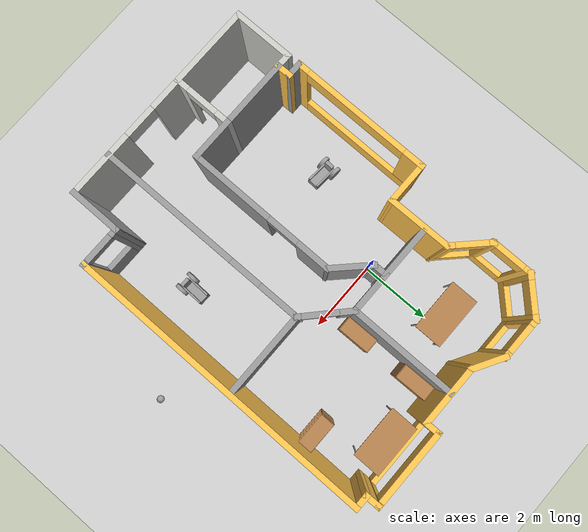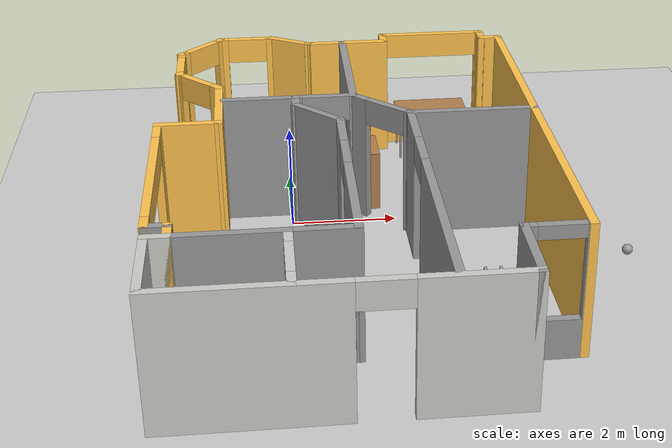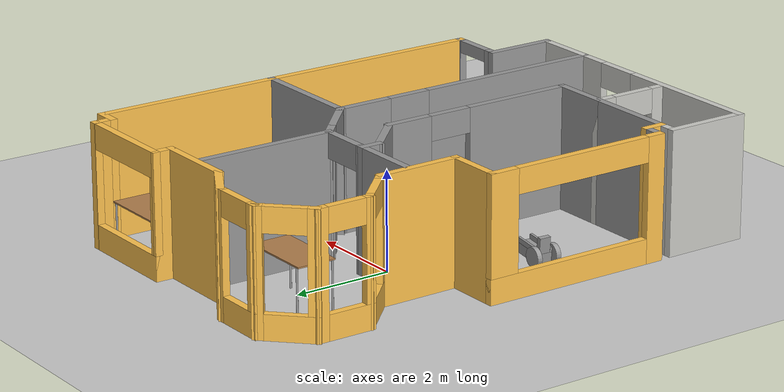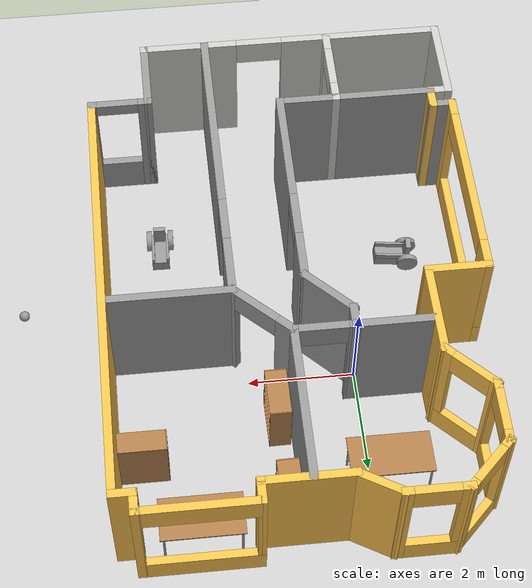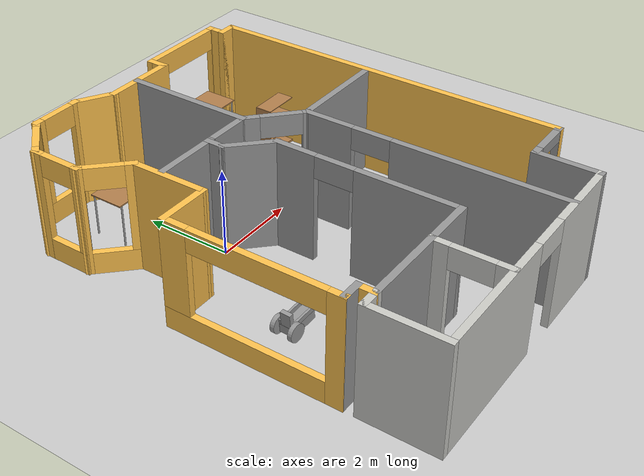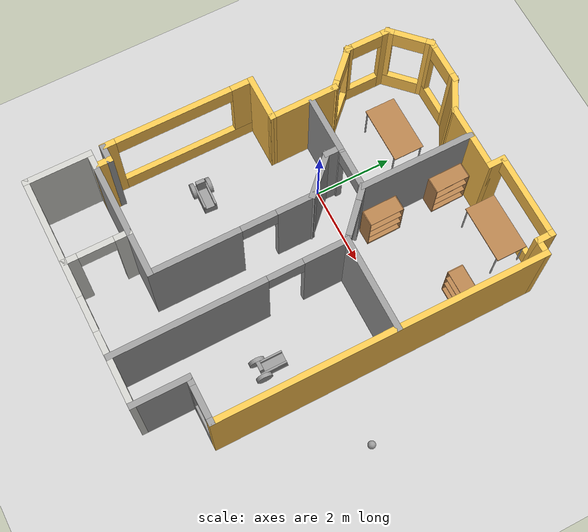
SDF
<sdf version="1.6">
 <world name="default">
  <plugin name="welcome_message" filename="libwelcome_message.so"/>
  <light name="sun" type="directional">
   <pose>0 0 10 0 -0 0</pose>
   <diffuse>0.8 0.8 0.8 1</diffuse>
   <specular>0.2 0.2 0.2 1</specular>
   <attenuation>
    <range>1000</range>
    <constant>0.9</constant>
    <linear>0.01</linear>
    <quadratic>0.001</quadratic>
   </attenuation>
   <direction>-0.5 0.1 -0.9</direction>
  </light>
  <model name="ground_plane">
   <static>1</static>
   <link name="link">
    <collision name="collision">
     <geometry><plane><normal>0 0 1</normal><size>100 100</size></plane></geometry>
     <surface><friction><ode><mu>100</mu><mu2>50</mu2></ode></friction></surface>
    </collision>
    <visual name="visual">
     <cast_shadows>0</cast_shadows>
     <geometry><plane><normal>0 0 1</normal><size>100 100</size></plane></geometry>
     <material>
      <script><uri>file://media/materials/scripts/gazebo.material</uri><name>Gazebo/Grey</name></script>
     </material>
    </visual>
   </link>
  </model>
  <gravity>0 0 -9.8</gravity>
  <magnetic_field>6e-06 2.3e-05 -4.2e-05</magnetic_field>
  <atmosphere type="adiabatic"/>
  <physics name="default_physics" default="0" type="ode">
   <max_step_size>0.001</max_step_size>
   <real_time_factor>1</real_time_factor>
   <real_time_update_rate>1000</real_time_update_rate>
  </physics>
  <scene><ambient>0.4 0.4 0.4 1</ambient><background>0.7 0.7 0.7 1</background><shadows>1</shadows></scene>
  <spherical_coordinates>
   <surface_model>EARTH_WGS84</surface_model>
   <latitude_deg>0</latitude_deg>
   <longitude_deg>0</longitude_deg>
   <elevation>0</elevation>
   <heading_deg>0</heading_deg>
  </spherical_coordinates>
  <model name="Building">
   <pose>1.08481 -1.31899 0 0 -0 0</pose>
   <link name="Wall_0">
    <pose>-0.54 -5.07803 0 0 -0 0</pose>
    <visual name="Wall_0_Visual_0">
     <pose>-1.40972 0 1.25 0 -0 0</pose>
     <geometry><box><size>3.18055 0.15 2.5</size></box></geometry>
     <material>
      <script><uri>file://media/materials/scripts/gazebo.material</uri><name>Gazebo/CeilingTiled</name></script>
      <ambient>1 1 1 1</ambient>
     </material>
     <meta><layer>0</layer></meta>
    </visual>
    <collision name="Wall_0_Collision_0">
     <geometry><box><size>3.18055 0.15 2.5</size></box></geometry>
     <pose>-1.40972 0 1.25 0 -0 0</pose>
    </collision>
    <visual name="Wall_0_Visual_1">
     <pose>2.04028 0 1.25 0 -0 0</pose>
     <geometry><box><size>1.91945 0.15 2.5</size></box></geometry>
     <material>
      <script><uri>file://media/materials/scripts/gazebo.material</uri><name>Gazebo/CeilingTiled</name></script>
      <ambient>1 1 1 1</ambient>
     </material>
     <meta><layer>0</layer></meta>
    </visual>
    <collision name="Wall_0_Collision_1">
     <geometry><box><size>1.91945 0.15 2.5</size></box></geometry>
     <pose>2.04028 0 1.25 0 -0 0</pose>
    </collision>
    <visual name="Wall_0_Visual_2">
     <pose>0.630554 0 2.25 0 -0 0</pose>
     <geometry><box><size>0.9 0.15 0.5</size></box></geometry>
     <material>
      <script><uri>file://media/materials/scripts/gazebo.material</uri><name>Gazebo/CeilingTiled</name></script>
      <ambient>1 1 1 1</ambient>
     </material>
     <meta><layer>0</layer></meta>
    </visual>
    <collision name="Wall_0_Collision_2">
     <geometry><box><size>0.9 0.15 0.5</size></box></geometry>
     <pose>0.630554 0 2.25 0 -0 0</pose>
    </collision>
   </link>
   <link name="Wall_1">
    <collision name="Wall_1_Collision">
     <geometry><box><size>1.5 0.15 2.5</size></box></geometry>
     <pose>0 0 1.25 0 -0 0</pose>
    </collision>
    <visual name="Wall_1_Visual">
     <pose>0 0 1.25 0 -0 0</pose>
     <geometry><box><size>1.5 0.15 2.5</size></box></geometry>
     <material>
      <script><uri>file://media/materials/scripts/gazebo.material</uri><name>Gazebo/Grey</name></script>
      <ambient>1 1 1 1</ambient>
     </material>
     <meta><layer>0</layer></meta>
    </visual>
    <pose>2.385 -4.40303 0 0 -0 1.5708</pose>
   </link>
   <link name="Wall_10">
    <pose>-1.85112 5.04697 0 0 -0 3.14159</pose>
    <visual name="Wall_10_Visual_0">
     <pose>-0.517736 0 1.25 0 -0 0</pose>
     <geometry><box><size>0.214528 0.15 2.5</size></box></geometry>
     <material>
      <script><uri>file://media/materials/scripts/gazebo.material</uri><name>Gazebo/Grey</name></script>
      <ambient>1 0.764706 0.305882 1</ambient>
     </material>
     <meta><layer>0</layer></meta>
    </visual>
    <collision name="Wall_10_Collision_0">
     <geometry><box><size>0.214528 0.15 2.5</size></box></geometry>
     <pose>-0.517736 0 1.25 0 -0 0</pose>
    </collision>
    <visual name="Wall_10_Visual_1">
     <pose>0.107264 0 0.25 0 -0 0</pose>
     <geometry><box><size>1.03547 0.15 0.5</size></box></geometry>
     <material>
      <script><uri>file://media/materials/scripts/gazebo.material</uri><name>Gazebo/Grey</name></script>
      <ambient>1 0.764706 0.305882 1</ambient>
     </material>
     <meta><layer>0</layer></meta>
    </visual>
    <collision name="Wall_10_Collision_1">
     <geometry><box><size>1.03547 0.15 0.5</size></box></geometry>
     <pose>0.107264 0 0.25 0 -0 0</pose>
    </collision>
    <visual name="Wall_10_Visual_2">
     <pose>0.507264 0 1.5 0 -0 0</pose>
     <geometry><box><size>0.235472 0.15 2</size></box></geometry>
     <material>
      <script><uri>file://media/materials/scripts/gazebo.material</uri><name>Gazebo/Grey</name></script>
      <ambient>1 0.764706 0.305882 1</ambient>
     </material>
     <meta><layer>0</layer></meta>
    </visual>
    <collision name="Wall_10_Collision_2">
     <geometry><box><size>0.235472 0.15 2</size></box></geometry>
     <pose>0.507264 0 1.5 0 -0 0</pose>
    </collision>
    <visual name="Wall_10_Visual_3">
     <pose>-0.010472 0 2.25 0 -0 0</pose>
     <geometry><box><size>0.8 0.15 0.5</size></box></geometry>
     <material>
      <script><uri>file://media/materials/scripts/gazebo.material</uri><name>Gazebo/Grey</name></script>
      <ambient>1 0.764706 0.305882 1</ambient>
     </material>
     <meta><layer>0</layer></meta>
    </visual>
    <collision name="Wall_10_Collision_3">
     <geometry><box><size>0.8 0.15 0.5</size></box></geometry>
     <pose>-0.010472 0 2.25 0 -0 0</pose>
    </collision>
   </link>
   <link name="Wall_11">
    <pose>-2.79003 4.65806 0 0 0 -2.35619</pose>
    <visual name="Wall_11_Visual_0">
     <pose>-0.516833 0 1.25 0 -0 0</pose>
     <geometry><box><size>0.216334 0.15 2.5</size></box></geometry>
     <material>
      <script><uri>file://media/materials/scripts/gazebo.material</uri><name>Gazebo/Grey</name></script>
      <ambient>1 0.764706 0.305882 1</ambient>
     </material>
     <meta><layer>0</layer></meta>
    </visual>
    <collision name="Wall_11_Collision_0">
     <geometry><box><size>0.216334 0.15 2.5</size></box></geometry>
     <pose>-0.516833 0 1.25 0 -0 0</pose>
    </collision>
    <visual name="Wall_11_Visual_1">
     <pose>0.108167 0 0.25 0 -0 0</pose>
     <geometry><box><size>1.03367 0.15 0.5</size></box></geometry>
     <material>
      <script><uri>file://media/materials/scripts/gazebo.material</uri><name>Gazebo/Grey</name></script>
      <ambient>1 0.764706 0.305882 1</ambient>
     </material>
     <meta><layer>0</layer></meta>
    </visual>
    <collision name="Wall_11_Collision_1">
     <geometry><box><size>1.03367 0.15 0.5</size></box></geometry>
     <pose>0.108167 0 0.25 0 -0 0</pose>
    </collision>
    <visual name="Wall_11_Visual_2">
     <pose>0.508167 0 1.5 0 -0 0</pose>
     <geometry><box><size>0.233666 0.15 2</size></box></geometry>
     <material>
      <script><uri>file://media/materials/scripts/gazebo.material</uri><name>Gazebo/Grey</name></script>
      <ambient>1 0.764706 0.305882 1</ambient>
     </material>
     <meta><layer>0</layer></meta>
    </visual>
    <collision name="Wall_11_Collision_2">
     <geometry><box><size>0.233666 0.15 2</size></box></geometry>
     <pose>0.508167 0 1.5 0 -0 0</pose>
    </collision>
    <visual name="Wall_11_Visual_3">
     <pose>-0.008666 0 2.25 0 -0 0</pose>
     <geometry><box><size>0.8 0.15 0.5</size></box></geometry>
     <material>
      <script><uri>file://media/materials/scripts/gazebo.material</uri><name>Gazebo/Grey</name></script>
      <ambient>1 0.764706 0.305882 1</ambient>
     </material>
     <meta><layer>0</layer></meta>
    </visual>
    <collision name="Wall_11_Collision_3">
     <geometry><box><size>0.8 0.15 0.5</size></box></geometry>
     <pose>-0.008666 0 2.25 0 -0 0</pose>
    </collision>
   </link>
   <link name="Wall_12">
    <pose>-3.17894 3.71915 0 0 0 -1.5708</pose>
    <visual name="Wall_12_Visual_0">
     <pose>-0.493695 0 1.25 0 -0 0</pose>
     <geometry><box><size>0.262609 0.15 2.5</size></box></geometry>
     <material>
      <script><uri>file://media/materials/scripts/gazebo.material</uri><name>Gazebo/Grey</name></script>
      <ambient>1 0.764706 0.305882 1</ambient>
     </material>
     <meta><layer>0</layer></meta>
    </visual>
    <collision name="Wall_12_Collision_0">
     <geometry><box><size>0.262609 0.15 2.5</size></box></geometry>
     <pose>-0.493695 0 1.25 0 -0 0</pose>
    </collision>
    <visual name="Wall_12_Visual_1">
     <pose>0.131305 0 0.25 0 -0 0</pose>
     <geometry><box><size>0.987391 0.15 0.5</size></box></geometry>
     <material>
      <script><uri>file://media/materials/scripts/gazebo.material</uri><name>Gazebo/Grey</name></script>
      <ambient>1 0.764706 0.305882 1</ambient>
     </material>
     <meta><layer>0</layer></meta>
    </visual>
    <collision name="Wall_12_Collision_1">
     <geometry><box><size>0.987391 0.15 0.5</size></box></geometry>
     <pose>0.131305 0 0.25 0 -0 0</pose>
    </collision>
    <visual name="Wall_12_Visual_2">
     <pose>0.531305 0 1.5 0 -0 0</pose>
     <geometry><box><size>0.187391 0.15 2</size></box></geometry>
     <material>
      <script><uri>file://media/materials/scripts/gazebo.material</uri><name>Gazebo/Grey</name></script>
      <ambient>1 0.764706 0.305882 1</ambient>
     </material>
     <meta><layer>0</layer></meta>
    </visual>
    <collision name="Wall_12_Collision_2">
     <geometry><box><size>0.187391 0.15 2</size></box></geometry>
     <pose>0.531305 0 1.5 0 -0 0</pose>
    </collision>
    <visual name="Wall_12_Visual_3">
     <pose>0.037609 0 2.25 0 -0 0</pose>
     <geometry><box><size>0.8 0.15 0.5</size></box></geometry>
     <material>
      <script><uri>file://media/materials/scripts/gazebo.material</uri><name>Gazebo/Grey</name></script>
      <ambient>1 0.764706 0.305882 1</ambient>
     </material>
     <meta><layer>0</layer></meta>
    </visual>
    <collision name="Wall_12_Collision_3">
     <geometry><box><size>0.8 0.15 0.5</size></box></geometry>
     <pose>0.037609 0 2.25 0 -0 0</pose>
    </collision>
   </link>
   <link name="Wall_13">
    <pose>-2.79003 2.78024 0 0 0 -0.785398</pose>
    <visual name="Wall_13_Visual_0">
     <pose>-0.532603 0 1.25 0 -0 0</pose>
     <geometry><box><size>0.184794 0.15 2.5</size></box></geometry>
     <material>
      <script><uri>file://media/materials/scripts/gazebo.material</uri><name>Gazebo/Grey</name></script>
      <ambient>1 0.764706 0.305882 1</ambient>
     </material>
     <meta><layer>0</layer></meta>
    </visual>
    <collision name="Wall_13_Collision_0">
     <geometry><box><size>0.184794 0.15 2.5</size></box></geometry>
     <pose>-0.532603 0 1.25 0 -0 0</pose>
    </collision>
    <visual name="Wall_13_Visual_1">
     <pose>0.092397 0 0.25 0 -0 0</pose>
     <geometry><box><size>1.06521 0.15 0.5</size></box></geometry>
     <material>
      <script><uri>file://media/materials/scripts/gazebo.material</uri><name>Gazebo/Grey</name></script>
      <ambient>1 0.764706 0.305882 1</ambient>
     </material>
     <meta><layer>0</layer></meta>
    </visual>
    <collision name="Wall_13_Collision_1">
     <geometry><box><size>1.06521 0.15 0.5</size></box></geometry>
     <pose>0.092397 0 0.25 0 -0 0</pose>
    </collision>
    <visual name="Wall_13_Visual_2">
     <pose>0.492397 0 1.5 0 -0 0</pose>
     <geometry><box><size>0.265206 0.15 2</size></box></geometry>
     <material>
      <script><uri>file://media/materials/scripts/gazebo.material</uri><name>Gazebo/Grey</name></script>
      <ambient>1 0.764706 0.305882 1</ambient>
     </material>
     <meta><layer>0</layer></meta>
    </visual>
    <collision name="Wall_13_Collision_2">
     <geometry><box><size>0.265206 0.15 2</size></box></geometry>
     <pose>0.492397 0 1.5 0 -0 0</pose>
    </collision>
    <visual name="Wall_13_Visual_3">
     <pose>-0.040206 0 2.25 0 -0 0</pose>
     <geometry><box><size>0.8 0.15 0.5</size></box></geometry>
     <material>
      <script><uri>file://media/materials/scripts/gazebo.material</uri><name>Gazebo/Grey</name></script>
      <ambient>1 0.764706 0.305882 1</ambient>
     </material>
     <meta><layer>0</layer></meta>
    </visual>
    <collision name="Wall_13_Collision_3">
     <geometry><box><size>0.8 0.15 0.5</size></box></geometry>
     <pose>-0.040206 0 2.25 0 -0 0</pose>
    </collision>
   </link>
   <link name="Wall_14">
    <collision name="Wall_14_Collision">
     <geometry><box><size>1.81944 0.15 2.5</size></box></geometry>
     <pose>0 0 1.25 0 -0 0</pose>
    </collision>
    <visual name="Wall_14_Visual">
     <pose>0 0 1.25 0 -0 0</pose>
     <geometry><box><size>1.81944 0.15 2.5</size></box></geometry>
     <material>
      <script><uri>file://media/materials/scripts/gazebo.material</uri><name>Gazebo/Grey</name></script>
      <ambient>1 0.764706 0.305882 1</ambient>
     </material>
     <meta><layer>0</layer></meta>
    </visual>
    <pose>-2.39306 1.55665 0 0 0 -1.56114</pose>
   </link>
   <link name="Wall_16">
    <collision name="Wall_16_Collision">
     <geometry><box><size>1.75 0.15 2.5</size></box></geometry>
     <pose>0 0 1.25 0 -0 0</pose>
    </collision>
    <visual name="Wall_16_Visual">
     <pose>0 0 1.25 0 -0 0</pose>
     <geometry><box><size>1.75 0.15 2.5</size></box></geometry>
     <material>
      <script><uri>file://media/materials/scripts/gazebo.material</uri><name>Gazebo/CeilingTiled</name></script>
      <ambient>1 0.764706 0.305882 1</ambient>
     </material>
     <meta><layer>0</layer></meta>
    </visual>
    <pose>-3.465 -4.27803 0 0 -0 1.5708</pose>
   </link>
   <link name="Wall_17">
    <collision name="Wall_17_Collision">
     <geometry><box><size>0.5 0.15 2.5</size></box></geometry>
     <pose>0 0 1.25 0 -0 0</pose>
    </collision>
    <visual name="Wall_17_Visual">
     <pose>0 0 1.25 0 -0 0</pose>
     <geometry><box><size>0.5 0.15 2.5</size></box></geometry>
     <material>
      <script><uri>file://media/materials/scripts/gazebo.material</uri><name>Gazebo/CeilingTiled</name></script>
      <ambient>1 0.764706 0.305882 1</ambient>
     </material>
     <meta><layer>0</layer></meta>
    </visual>
    <pose>-3.29 -3.47803 0 0 -0 0</pose>
   </link>
   <link name="Wall_18">
    <collision name="Wall_18_Collision">
     <geometry><box><size>0.5 0.15 2.5</size></box></geometry>
     <pose>0 0 1.25 0 -0 0</pose>
    </collision>
    <visual name="Wall_18_Visual">
     <pose>0 0 1.25 0 -0 0</pose>
     <geometry><box><size>0.5 0.15 2.5</size></box></geometry>
     <material>
      <script><uri>file://media/materials/scripts/gazebo.material</uri><name>Gazebo/Grey</name></script>
      <ambient>1 0.764706 0.305882 1</ambient>
     </material>
     <meta><layer>0</layer></meta>
    </visual>
    <pose>-3.115 -3.30303 0 0 -0 1.5708</pose>
   </link>
   <link name="Wall_19">
    <collision name="Wall_19_Collision">
     <geometry><box><size>0.5 0.15 2.5</size></box></geometry>
     <pose>0 0 1.25 0 -0 0</pose>
    </collision>
    <visual name="Wall_19_Visual">
     <pose>0 0 1.25 0 -0 0</pose>
     <geometry><box><size>0.5 0.15 2.5</size></box></geometry>
     <material>
      <script><uri>file://media/materials/scripts/gazebo.material</uri><name>Gazebo/Grey</name></script>
      <ambient>1 1 1 1</ambient>
     </material>
     <meta><layer>0</layer></meta>
    </visual>
    <pose>-3.29 -3.12803 0 0 -0 3.14159</pose>
   </link>
   <link name="Wall_2">
    <pose>2.935 -3.72803 0 0 -0 0</pose>
    <visual name="Wall_2_Visual_0">
     <pose>-0.486696 0 1.25 0 -0 0</pose>
     <geometry><box><size>0.276608 0.15 2.5</size></box></geometry>
     <material>
      <script><uri>file://media/materials/scripts/gazebo.material</uri><name>Gazebo/Grey</name></script>
      <ambient>1 1 1 1</ambient>
     </material>
     <meta><layer>0</layer></meta>
    </visual>
    <collision name="Wall_2_Collision_0">
     <geometry><box><size>0.276608 0.15 2.5</size></box></geometry>
     <pose>-0.486696 0 1.25 0 -0 0</pose>
    </collision>
    <visual name="Wall_2_Visual_1">
     <pose>0.138304 0 0.375 0 -0 0</pose>
     <geometry><box><size>0.973392 0.15 0.75</size></box></geometry>
     <material>
      <script><uri>file://media/materials/scripts/gazebo.material</uri><name>Gazebo/Grey</name></script>
      <ambient>1 1 1 1</ambient>
     </material>
     <meta><layer>0</layer></meta>
    </visual>
    <collision name="Wall_2_Collision_1">
     <geometry><box><size>0.973392 0.15 0.75</size></box></geometry>
     <pose>0.138304 0 0.375 0 -0 0</pose>
    </collision>
    <visual name="Wall_2_Visual_2">
     <pose>0.538304 0 1.625 0 -0 0</pose>
     <geometry><box><size>0.173392 0.15 1.75</size></box></geometry>
     <material>
      <script><uri>file://media/materials/scripts/gazebo.material</uri><name>Gazebo/Grey</name></script>
      <ambient>1 1 1 1</ambient>
     </material>
     <meta><layer>0</layer></meta>
    </visual>
    <collision name="Wall_2_Collision_2">
     <geometry><box><size>0.173392 0.15 1.75</size></box></geometry>
     <pose>0.538304 0 1.625 0 -0 0</pose>
    </collision>
    <visual name="Wall_2_Visual_3">
     <pose>0.051608 0 2.375 0 -0 0</pose>
     <geometry><box><size>0.8 0.15 0.25</size></box></geometry>
     <material>
      <script><uri>file://media/materials/scripts/gazebo.material</uri><name>Gazebo/Grey</name></script>
      <ambient>1 1 1 1</ambient>
     </material>
     <meta><layer>0</layer></meta>
    </visual>
    <collision name="Wall_2_Collision_3">
     <geometry><box><size>0.8 0.15 0.25</size></box></geometry>
     <pose>0.051608 0 2.375 0 -0 0</pose>
    </collision>
   </link>
   <link name="Wall_20">
    <pose>-3.485 -1.20303 0 0 -0 1.5708</pose>
    <visual name="Wall_20_Visual_0">
     <pose>-1.80879 0 1.25 0 -0 0</pose>
     <geometry><box><size>0.382416 0.15 2.5</size></box></geometry>
     <material>
      <script><uri>file://media/materials/scripts/gazebo.material</uri><name>Gazebo/Grey</name></script>
      <ambient>1 0.764706 0.305882 1</ambient>
     </material>
     <meta><layer>0</layer></meta>
    </visual>
    <collision name="Wall_20_Collision_0">
     <geometry><box><size>0.382416 0.15 2.5</size></box></geometry>
     <pose>-1.80879 0 1.25 0 -0 0</pose>
    </collision>
    <visual name="Wall_20_Visual_1">
     <pose>0.191208 0 0.25 0 -0 0</pose>
     <geometry><box><size>3.61758 0.15 0.5</size></box></geometry>
     <material>
      <script><uri>file://media/materials/scripts/gazebo.material</uri><name>Gazebo/Grey</name></script>
      <ambient>1 0.764706 0.305882 1</ambient>
     </material>
     <meta><layer>0</layer></meta>
    </visual>
    <collision name="Wall_20_Collision_1">
     <geometry><box><size>3.61758 0.15 0.5</size></box></geometry>
     <pose>0.191208 0 0.25 0 -0 0</pose>
    </collision>
    <visual name="Wall_20_Visual_2">
     <pose>1.69121 0 1.5 0 -0 0</pose>
     <geometry><box><size>0.617584 0.15 2</size></box></geometry>
     <material>
      <script><uri>file://media/materials/scripts/gazebo.material</uri><name>Gazebo/Grey</name></script>
      <ambient>1 0.764706 0.305882 1</ambient>
     </material>
     <meta><layer>0</layer></meta>
    </visual>
    <collision name="Wall_20_Collision_2">
     <geometry><box><size>0.617584 0.15 2</size></box></geometry>
     <pose>1.69121 0 1.5 0 -0 0</pose>
    </collision>
    <visual name="Wall_20_Visual_3">
     <pose>-0.117584 0 2.25 0 -0 0</pose>
     <geometry><box><size>3 0.15 0.5</size></box></geometry>
     <material>
      <script><uri>file://media/materials/scripts/gazebo.material</uri><name>Gazebo/Grey</name></script>
      <ambient>1 0.764706 0.305882 1</ambient>
     </material>
     <meta><layer>0</layer></meta>
    </visual>
    <collision name="Wall_20_Collision_3">
     <geometry><box><size>3 0.15 0.5</size></box></geometry>
     <pose>-0.117584 0 2.25 0 -0 0</pose>
    </collision>
   </link>
   <link name="Wall_22">
    <collision name="Wall_22_Collision">
     <geometry><box><size>1.25 0.15 2.5</size></box></geometry>
     <pose>0 0 1.25 0 -0 0</pose>
    </collision>
    <visual name="Wall_22_Visual">
     <pose>0 0 1.25 0 -0 0</pose>
     <geometry><box><size>1.25 0.15 2.5</size></box></geometry>
     <material>
      <script><uri>file://media/materials/scripts/gazebo.material</uri><name>Gazebo/Grey</name></script>
      <ambient>1 0.764706 0.305882 1</ambient>
     </material>
     <meta><layer>0</layer></meta>
    </visual>
    <pose>-2.935 0.721967 0 0 -0 0</pose>
   </link>
   <link name="Wall_26">
    <collision name="Wall_26_Collision">
     <geometry><box><size>2 0.15 2.5</size></box></geometry>
     <pose>0 0 1.25 0 -0 0</pose>
    </collision>
    <visual name="Wall_26_Visual">
     <pose>0 0 1.25 0 -0 0</pose>
     <geometry><box><size>2 0.15 2.5</size></box></geometry>
     <material>
      <script><uri>file://media/materials/scripts/gazebo.material</uri><name>Gazebo/Grey</name></script>
      <ambient>1 1 1 1</ambient>
     </material>
     <meta><layer>0</layer></meta>
    </visual>
    <pose>-2.19 -3.47803 0 0 -0 0</pose>
   </link>
   <link name="Wall_27">
    <pose>-1.265 -4.27803 0 0 0 -1.5708</pose>
    <visual name="Wall_27_Visual_0">
     <pose>-0.653637 0 1.25 0 -0 0</pose>
     <geometry><box><size>0.442727 0.15 2.5</size></box></geometry>
     <material>
      <script><uri>file://media/materials/scripts/gazebo.material</uri><name>Gazebo/CeilingTiled</name></script>
      <ambient>1 1 1 1</ambient>
     </material>
     <meta><layer>0</layer></meta>
    </visual>
    <collision name="Wall_27_Collision_0">
     <geometry><box><size>0.442727 0.15 2.5</size></box></geometry>
     <pose>-0.653637 0 1.25 0 -0 0</pose>
    </collision>
    <visual name="Wall_27_Visual_1">
     <pose>0.671363 0 1.25 0 -0 0</pose>
     <geometry><box><size>0.407273 0.15 2.5</size></box></geometry>
     <material>
      <script><uri>file://media/materials/scripts/gazebo.material</uri><name>Gazebo/CeilingTiled</name></script>
      <ambient>1 1 1 1</ambient>
     </material>
     <meta><layer>0</layer></meta>
    </visual>
    <collision name="Wall_27_Collision_1">
     <geometry><box><size>0.407273 0.15 2.5</size></box></geometry>
     <pose>0.671363 0 1.25 0 -0 0</pose>
    </collision>
    <visual name="Wall_27_Visual_2">
     <pose>0.017727 0 2.25 0 -0 0</pose>
     <geometry><box><size>0.9 0.15 0.5</size></box></geometry>
     <material>
      <script><uri>file://media/materials/scripts/gazebo.material</uri><name>Gazebo/CeilingTiled</name></script>
      <ambient>1 1 1 1</ambient>
     </material>
     <meta><layer>0</layer></meta>
    </visual>
    <collision name="Wall_27_Collision_2">
     <geometry><box><size>0.9 0.15 0.5</size></box></geometry>
     <pose>0.017727 0 2.25 0 -0 0</pose>
    </collision>
   </link>
   <link name="Wall_29">
    <collision name="Wall_29_Collision">
     <geometry><box><size>1.25 0.15 2.5</size></box></geometry>
     <pose>0 0 1.25 0 -0 0</pose>
    </collision>
    <visual name="Wall_29_Visual">
     <pose>0 0 1.25 0 -0 0</pose>
     <geometry><box><size>1.25 0.15 2.5</size></box></geometry>
     <material>
      <script><uri>file://media/materials/scripts/gazebo.material</uri><name>Gazebo/Grey</name></script>
      <ambient>1 1 1 1</ambient>
     </material>
     <meta><layer>0</layer></meta>
    </visual>
    <pose>-0.715 -3.47803 0 0 -0 0</pose>
   </link>
   <link name="Wall_3">
    <collision name="Wall_3_Collision">
     <geometry><box><size>8.5 0.15 2.5</size></box></geometry>
     <pose>0 0 1.25 0 -0 0</pose>
    </collision>
    <visual name="Wall_3_Visual">
     <pose>0 0 1.25 0 -0 0</pose>
     <geometry><box><size>8.5 0.15 2.5</size></box></geometry>
     <material>
      <script><uri>file://media/materials/scripts/gazebo.material</uri><name>Gazebo/Grey</name></script>
      <ambient>1 0.764706 0.305882 1</ambient>
     </material>
     <meta><layer>0</layer></meta>
    </visual>
    <pose>3.485 0.446967 0 0 -0 1.5708</pose>
   </link>
   <link name="Wall_30">
    <pose>-0.165 -1.42803 0 0 -0 1.5708</pose>
    <visual name="Wall_30_Visual_0">
     <pose>-0.949214 0 1.25 0 -0 0</pose>
     <geometry><box><size>2.35157 0.15 2.5</size></box></geometry>
     <material>
      <script><uri>file://media/materials/scripts/gazebo.material</uri><name>Gazebo/Grey</name></script>
      <ambient>1 1 1 1</ambient>
     </material>
     <meta><layer>0</layer></meta>
    </visual>
    <collision name="Wall_30_Collision_0">
     <geometry><box><size>2.35157 0.15 2.5</size></box></geometry>
     <pose>-0.949214 0 1.25 0 -0 0</pose>
    </collision>
    <visual name="Wall_30_Visual_1">
     <pose>1.62579 0 1.25 0 -0 0</pose>
     <geometry><box><size>0.998427 0.15 2.5</size></box></geometry>
     <material>
      <script><uri>file://media/materials/scripts/gazebo.material</uri><name>Gazebo/Grey</name></script>
      <ambient>1 1 1 1</ambient>
     </material>
     <meta><layer>0</layer></meta>
    </visual>
    <collision name="Wall_30_Collision_1">
     <geometry><box><size>0.998427 0.15 2.5</size></box></geometry>
     <pose>1.62579 0 1.25 0 -0 0</pose>
    </collision>
    <visual name="Wall_30_Visual_2">
     <pose>0.676573 0 2.25 0 -0 0</pose>
     <geometry><box><size>0.9 0.15 0.5</size></box></geometry>
     <material>
      <script><uri>file://media/materials/scripts/gazebo.material</uri><name>Gazebo/Grey</name></script>
      <ambient>1 1 1 1</ambient>
     </material>
     <meta><layer>0</layer></meta>
    </visual>
    <collision name="Wall_30_Collision_2">
     <geometry><box><size>0.9 0.15 0.5</size></box></geometry>
     <pose>0.676573 0 2.25 0 -0 0</pose>
    </collision>
   </link>
   <link name="Wall_31">
    <collision name="Wall_31_Collision">
     <geometry><box><size>1.25 0.15 2.5</size></box></geometry>
     <pose>0 0 1.25 0 -0 0</pose>
    </collision>
    <visual name="Wall_31_Visual">
     <pose>0 0 1.25 0 -0 0</pose>
     <geometry><box><size>1.25 0.15 2.5</size></box></geometry>
     <material>
      <script><uri>file://media/materials/scripts/gazebo.material</uri><name>Gazebo/Grey</name></script>
      <ambient>1 1 1 1</ambient>
     </material>
     <meta><layer>0</layer></meta>
    </visual>
    <pose>-0.553909 1.01088 0 0 -0 2.35619</pose>
   </link>
   <link name="Wall_32">
    <collision name="Wall_32_Collision">
     <geometry><box><size>0.5 0.15 2.5</size></box></geometry>
     <pose>0 0 1.25 0 -0 0</pose>
    </collision>
    <visual name="Wall_32_Visual">
     <pose>0 0 1.25 0 -0 0</pose>
     <geometry><box><size>0.5 0.15 2.5</size></box></geometry>
     <material>
      <script><uri>file://media/materials/scripts/gazebo.material</uri><name>Gazebo/Grey</name></script>
      <ambient>1 1 1 1</ambient>
     </material>
     <meta><layer>0</layer></meta>
    </visual>
    <pose>-0.942818 1.57479 0 0 -0 1.5708</pose>
   </link>
   <link name="Wall_33">
    <collision name="Wall_33_Collision">
     <geometry><box><size>1.5 0.15 2.5</size></box></geometry>
     <pose>0 0 1.25 0 -0 0</pose>
    </collision>
    <visual name="Wall_33_Visual">
     <pose>0 0 1.25 0 -0 0</pose>
     <geometry><box><size>1.5 0.15 2.5</size></box></geometry>
     <material>
      <script><uri>file://media/materials/scripts/gazebo.material</uri><name>Gazebo/Grey</name></script>
      <ambient>1 1 1 1</ambient>
     </material>
     <meta><layer>0</layer></meta>
    </visual>
    <pose>-1.61782 1.74978 0 0 -0 3.14159</pose>
   </link>
   <link name="Wall_35">
    <pose>-0.392818 1.74978 0 0 -0 0</pose>
    <visual name="Wall_35_Visual_0">
     <pose>-0.524612 0 1.25 0 -0 0</pose>
     <geometry><box><size>0.200777 0.15 2.5</size></box></geometry>
     <material>
      <script><uri>file://media/materials/scripts/gazebo.material</uri><name>Gazebo/Grey</name></script>
      <ambient>1 1 1 1</ambient>
     </material>
     <meta><layer>0</layer></meta>
    </visual>
    <collision name="Wall_35_Collision_0">
     <geometry><box><size>0.200777 0.15 2.5</size></box></geometry>
     <pose>-0.524612 0 1.25 0 -0 0</pose>
    </collision>
    <visual name="Wall_35_Visual_1">
     <pose>0.550388 0 1.25 0 -0 0</pose>
     <geometry><box><size>0.149223 0.15 2.5</size></box></geometry>
     <material>
      <script><uri>file://media/materials/scripts/gazebo.material</uri><name>Gazebo/Grey</name></script>
      <ambient>1 1 1 1</ambient>
     </material>
     <meta><layer>0</layer></meta>
    </visual>
    <collision name="Wall_35_Collision_1">
     <geometry><box><size>0.149223 0.15 2.5</size></box></geometry>
     <pose>0.550388 0 1.25 0 -0 0</pose>
    </collision>
    <visual name="Wall_35_Visual_2">
     <pose>0.025777 0 2.25 0 -0 0</pose>
     <geometry><box><size>0.9 0.15 0.5</size></box></geometry>
     <material>
      <script><uri>file://media/materials/scripts/gazebo.material</uri><name>Gazebo/Grey</name></script>
      <ambient>1 1 1 1</ambient>
     </material>
     <meta><layer>0</layer></meta>
    </visual>
    <collision name="Wall_35_Collision_2">
     <geometry><box><size>0.9 0.15 0.5</size></box></geometry>
     <pose>0.025777 0 2.25 0 -0 0</pose>
    </collision>
   </link>
   <link name="Wall_36">
    <collision name="Wall_36_Collision">
     <geometry><box><size>3 0.15 2.5</size></box></geometry>
     <pose>0 0 1.25 0 -0 0</pose>
    </collision>
    <visual name="Wall_36_Visual">
     <pose>0 0 1.25 0 -0 0</pose>
     <geometry><box><size>3 0.15 2.5</size></box></geometry>
     <material>
      <script><uri>file://media/materials/scripts/gazebo.material</uri><name>Gazebo/Grey</name></script>
      <ambient>1 1 1 1</ambient>
     </material>
     <meta><layer>0</layer></meta>
    </visual>
    <pose>0.157182 3.17478 0 0 -0 1.5708</pose>
   </link>
   <link name="Wall_38">
    <pose>1.16672 -2.12643 0 0 -0 1.57466</pose>
    <visual name="Wall_38_Visual_0">
     <pose>-1.04783 0 1.25 0 -0 0</pose>
     <geometry><box><size>3.93688 0.15 2.5</size></box></geometry>
     <material>
      <script><uri>file://media/materials/scripts/gazebo.material</uri><name>Gazebo/Grey</name></script>
      <ambient>1 1 1 1</ambient>
     </material>
     <meta><layer>0</layer></meta>
    </visual>
    <collision name="Wall_38_Collision_0">
     <geometry><box><size>3.93688 0.15 2.5</size></box></geometry>
     <pose>-1.04783 0 1.25 0 -0 0</pose>
    </collision>
    <visual name="Wall_38_Visual_1">
     <pose>2.41844 0 1.25 0 -0 0</pose>
     <geometry><box><size>1.19567 0.15 2.5</size></box></geometry>
     <material>
      <script><uri>file://media/materials/scripts/gazebo.material</uri><name>Gazebo/Grey</name></script>
      <ambient>1 1 1 1</ambient>
     </material>
     <meta><layer>0</layer></meta>
    </visual>
    <collision name="Wall_38_Collision_1">
     <geometry><box><size>1.19567 0.15 2.5</size></box></geometry>
     <pose>2.41844 0 1.25 0 -0 0</pose>
    </collision>
    <visual name="Wall_38_Visual_2">
     <pose>1.37061 0 2.25 0 -0 0</pose>
     <geometry><box><size>0.9 0.15 0.5</size></box></geometry>
     <material>
      <script><uri>file://media/materials/scripts/gazebo.material</uri><name>Gazebo/Grey</name></script>
      <ambient>1 1 1 1</ambient>
     </material>
     <meta><layer>0</layer></meta>
    </visual>
    <collision name="Wall_38_Collision_2">
     <geometry><box><size>0.9 0.15 0.5</size></box></geometry>
     <pose>1.37061 0 2.25 0 -0 0</pose>
    </collision>
   </link>
   <link name="Wall_39">
    <pose>0.656263 1.2823 0 0 -0 2.38888</pose>
    <visual name="Wall_39_Visual_0">
     <pose>-0.666538 0 1.25 0 -0 0</pose>
     <geometry><box><size>0.184579 0.15 2.5</size></box></geometry>
     <material>
      <script><uri>file://media/materials/scripts/gazebo.material</uri><name>Gazebo/Grey</name></script>
      <ambient>1 1 1 1</ambient>
     </material>
     <meta><layer>0</layer></meta>
    </visual>
    <collision name="Wall_39_Collision_0">
     <geometry><box><size>0.184579 0.15 2.5</size></box></geometry>
     <pose>-0.666538 0 1.25 0 -0 0</pose>
    </collision>
    <visual name="Wall_39_Visual_1">
     <pose>0.542289 0 1.25 0 -0 0</pose>
     <geometry><box><size>0.433076 0.15 2.5</size></box></geometry>
     <material>
      <script><uri>file://media/materials/scripts/gazebo.material</uri><name>Gazebo/Grey</name></script>
      <ambient>1 1 1 1</ambient>
     </material>
     <meta><layer>0</layer></meta>
    </visual>
    <collision name="Wall_39_Collision_1">
     <geometry><box><size>0.433076 0.15 2.5</size></box></geometry>
     <pose>0.542289 0 1.25 0 -0 0</pose>
    </collision>
    <visual name="Wall_39_Visual_2">
     <pose>-0.124249 0 2.25 0 -0 0</pose>
     <geometry><box><size>0.9 0.15 0.5</size></box></geometry>
     <material>
      <script><uri>file://media/materials/scripts/gazebo.material</uri><name>Gazebo/Grey</name></script>
      <ambient>1 1 1 1</ambient>
     </material>
     <meta><layer>0</layer></meta>
    </visual>
    <collision name="Wall_39_Collision_2">
     <geometry><box><size>0.9 0.15 0.5</size></box></geometry>
     <pose>-0.124249 0 2.25 0 -0 0</pose>
    </collision>
   </link>
   <link name="Wall_4">
    <collision name="Wall_4_Collision">
     <geometry><box><size>0.5 0.15 2.5</size></box></geometry>
     <pose>0 0 1.25 0 -0 0</pose>
    </collision>
    <visual name="Wall_4_Visual">
     <pose>0 0 1.25 0 -0 0</pose>
     <geometry><box><size>0.5 0.15 2.5</size></box></geometry>
     <material>
      <script><uri>file://media/materials/scripts/gazebo.material</uri><name>Gazebo/Grey</name></script>
      <ambient>1 0.764706 0.305882 1</ambient>
     </material>
     <meta><layer>0</layer></meta>
    </visual>
    <pose>3.31 4.62197 0 0 -0 3.14159</pose>
   </link>
   <link name="Wall_41">
    <collision name="Wall_41_Collision">
     <geometry><box><size>2.47946 0.15 2.5</size></box></geometry>
     <pose>0 0 1.25 0 -0 0</pose>
    </collision>
    <visual name="Wall_41_Visual">
     <pose>0 0 1.25 0 -0 0</pose>
     <geometry><box><size>2.47946 0.15 2.5</size></box></geometry>
     <material>
      <script><uri>file://media/materials/scripts/gazebo.material</uri><name>Gazebo/Grey</name></script>
      <ambient>1 1 1 1</ambient>
     </material>
     <meta><layer>0</layer></meta>
    </visual>
    <pose>2.32007 0.817744 0 0 0 -0.000281</pose>
   </link>
   <link name="Wall_5">
    <collision name="Wall_5_Collision">
     <geometry><box><size>0.5 0.15 2.5</size></box></geometry>
     <pose>0 0 1.25 0 -0 0</pose>
    </collision>
    <visual name="Wall_5_Visual">
     <pose>0 0 1.25 0 -0 0</pose>
     <geometry><box><size>0.5 0.15 2.5</size></box></geometry>
     <material>
      <script><uri>file://media/materials/scripts/gazebo.material</uri><name>Gazebo/Grey</name></script>
      <ambient>1 0.764706 0.305882 1</ambient>
     </material>
     <meta><layer>0</layer></meta>
    </visual>
    <pose>3.135 4.79697 0 0 -0 1.5708</pose>
   </link>
   <link name="Wall_6">
    <pose>2.085 4.97197 0 0 -0 3.14159</pose>
    <visual name="Wall_6_Visual_0">
     <pose>-1.04107 0 1.25 0 -0 0</pose>
     <geometry><box><size>0.167856 0.15 2.5</size></box></geometry>
     <material>
      <script><uri>file://media/materials/scripts/gazebo.material</uri><name>Gazebo/Grey</name></script>
      <ambient>1 0.764706 0.305882 1</ambient>
     </material>
     <meta><layer>0</layer></meta>
    </visual>
    <collision name="Wall_6_Collision_0">
     <geometry><box><size>0.167856 0.15 2.5</size></box></geometry>
     <pose>-1.04107 0 1.25 0 -0 0</pose>
    </collision>
    <visual name="Wall_6_Visual_1">
     <pose>0.083928 0 0.25 0 -0 0</pose>
     <geometry><box><size>2.08214 0.15 0.5</size></box></geometry>
     <material>
      <script><uri>file://media/materials/scripts/gazebo.material</uri><name>Gazebo/Grey</name></script>
      <ambient>1 0.764706 0.305882 1</ambient>
     </material>
     <meta><layer>0</layer></meta>
    </visual>
    <collision name="Wall_6_Collision_1">
     <geometry><box><size>2.08214 0.15 0.5</size></box></geometry>
     <pose>0.083928 0 0.25 0 -0 0</pose>
    </collision>
    <visual name="Wall_6_Visual_2">
     <pose>1.08393 0 1.5 0 -0 0</pose>
     <geometry><box><size>0.082144 0.15 2</size></box></geometry>
     <material>
      <script><uri>file://media/materials/scripts/gazebo.material</uri><name>Gazebo/Grey</name></script>
      <ambient>1 0.764706 0.305882 1</ambient>
     </material>
     <meta><layer>0</layer></meta>
    </visual>
    <collision name="Wall_6_Collision_2">
     <geometry><box><size>0.082144 0.15 2</size></box></geometry>
     <pose>1.08393 0 1.5 0 -0 0</pose>
    </collision>
    <visual name="Wall_6_Visual_3">
     <pose>0.042856 0 2.25 0 -0 0</pose>
     <geometry><box><size>2 0.15 0.5</size></box></geometry>
     <material>
      <script><uri>file://media/materials/scripts/gazebo.material</uri><name>Gazebo/Grey</name></script>
      <ambient>1 0.764706 0.305882 1</ambient>
     </material>
     <meta><layer>0</layer></meta>
    </visual>
    <collision name="Wall_6_Collision_3">
     <geometry><box><size>2 0.15 0.5</size></box></geometry>
     <pose>0.042856 0 2.25 0 -0 0</pose>
    </collision>
   </link>
   <link name="Wall_7">
    <collision name="Wall_7_Collision">
     <geometry><box><size>0.5 0.15 2.5</size></box></geometry>
     <pose>0 0 1.25 0 -0 0</pose>
    </collision>
    <visual name="Wall_7_Visual">
     <pose>0 0 1.25 0 -0 0</pose>
     <geometry><box><size>0.5 0.15 2.5</size></box></geometry>
     <material>
      <script><uri>file://media/materials/scripts/gazebo.material</uri><name>Gazebo/Grey</name></script>
      <ambient>1 0.764706 0.305882 1</ambient>
     </material>
     <meta><layer>0</layer></meta>
    </visual>
    <pose>1.035 4.79697 0 0 0 -1.5708</pose>
   </link>
   <link name="Wall_8">
    <collision name="Wall_8_Collision">
     <geometry><box><size>1.75 0.15 2.5</size></box></geometry>
     <pose>0 0 1.25 0 -0 0</pose>
    </collision>
    <visual name="Wall_8_Visual">
     <pose>0 0 1.25 0 -0 0</pose>
     <geometry><box><size>1.75 0.15 2.5</size></box></geometry>
     <material>
      <script><uri>file://media/materials/scripts/gazebo.material</uri><name>Gazebo/Grey</name></script>
      <ambient>1 0.764706 0.305882 1</ambient>
     </material>
     <meta><layer>0</layer></meta>
    </visual>
    <pose>0.235 4.62197 0 0 -0 3.14159</pose>
   </link>
   <link name="Wall_9">
    <collision name="Wall_9_Collision">
     <geometry><box><size>1 0.15 2.5</size></box></geometry>
     <pose>0 0 1.25 0 -0 0</pose>
    </collision>
    <visual name="Wall_9_Visual">
     <pose>0 0 1.25 0 -0 0</pose>
     <geometry><box><size>1 0.15 2.5</size></box></geometry>
     <material>
      <script><uri>file://media/materials/scripts/gazebo.material</uri><name>Gazebo/Grey</name></script>
      <ambient>1 0.764706 0.305882 1</ambient>
     </material>
     <meta><layer>0</layer></meta>
    </visual>
    <pose>-0.933061 4.83447 0 0 -0 2.61799</pose>
   </link>
   <static>1</static>
  </model>
  <model name="bookshelf">
   <static>1</static>
   <link name="link">
    <inertial><mass>1</mass></inertial>
    <collision name="back">
     <pose>0 0.005 0.6 0 -0 0</pose>
     <geometry><box><size>0.9 0.01 1.2</size></box></geometry>
    </collision>
    <visual name="visual1">
     <pose>0 0.005 0.6 0 -0 0</pose>
     <geometry><box><size>0.9 0.01 1.2</size></box></geometry>
     <material>
      <script><uri>file://media/materials/scripts/gazebo.material</uri><name>Gazebo/Wood</name></script>
     </material>
    </visual>
    <collision name="left_side">
     <pose>0.45 -0.195 0.6 0 -0 0</pose>
     <geometry><box><size>0.02 0.4 1.2</size></box></geometry>
    </collision>
    <visual name="visual2">
     <pose>0.45 -0.195 0.6 0 -0 0</pose>
     <geometry><box><size>0.02 0.4 1.2</size></box></geometry>
     <material>
      <script><uri>file://media/materials/scripts/gazebo.material</uri><name>Gazebo/Wood</name></script>
     </material>
    </visual>
    <collision name="right_side">
     <pose>-0.45 -0.195 0.6 0 -0 0</pose>
     <geometry><box><size>0.02 0.4 1.2</size></box></geometry>
    </collision>
    <visual name="visual3">
     <pose>-0.45 -0.195 0.6 0 -0 0</pose>
     <geometry><box><size>0.02 0.4 1.2</size></box></geometry>
     <material>
      <script><uri>file://media/materials/scripts/gazebo.material</uri><name>Gazebo/Wood</name></script>
     </material>
    </visual>
    <collision name="bottom">
     <pose>0 -0.195 0.03 0 -0 0</pose>
     <geometry><box><size>0.88 0.4 0.06</size></box></geometry>
    </collision>
    <visual name="visual4">
     <pose>0 -0.195 0.03 0 -0 0</pose>
     <geometry><box><size>0.88 0.4 0.06</size></box></geometry>
     <material>
      <script><uri>file://media/materials/scripts/gazebo.material</uri><name>Gazebo/Wood</name></script>
     </material>
    </visual>
    <collision name="top">
     <pose>0 -0.195 1.19 0 -0 0</pose>
     <geometry><box><size>0.88 0.4 0.02</size></box></geometry>
    </collision>
    <visual name="visual5">
     <pose>0 -0.195 1.19 0 -0 0</pose>
     <geometry><box><size>0.88 0.4 0.02</size></box></geometry>
     <material>
      <script><uri>file://media/materials/scripts/gazebo.material</uri><name>Gazebo/Wood</name></script>
     </material>
    </visual>
    <collision name="low_shelf">
     <pose>0 -0.195 0.43 0 -0 0</pose>
     <geometry><box><size>0.88 0.4 0.02</size></box></geometry>
    </collision>
    <visual name="visual6">
     <pose>0 -0.195 0.43 0 -0 0</pose>
     <geometry><box><size>0.88 0.4 0.02</size></box></geometry>
     <material>
      <script><uri>file://media/materials/scripts/gazebo.material</uri><name>Gazebo/Wood</name></script>
     </material>
    </visual>
    <collision name="high_shelf">
     <pose>0 -0.195 0.8 0 -0 0</pose>
     <geometry><box><size>0.88 0.4 0.02</size></box></geometry>
    </collision>
    <visual name="visual7">
     <pose>0 -0.195 0.8 0 -0 0</pose>
     <geometry><box><size>0.88 0.4 0.02</size></box></geometry>
     <material>
      <script><uri>file://media/materials/scripts/gazebo.material</uri><name>Gazebo/Wood</name></script>
     </material>
    </visual>
   </link>
   <pose>1.33392 2.73117 0 0 -0 1.58719</pose>
  </model>
  <model name="bookshelf_0">
   <static>1</static>
   <link name="link">
    <inertial><mass>1</mass></inertial>
    <collision name="back">
     <pose>0 0.005 0.6 0 -0 0</pose>
     <geometry><box><size>0.9 0.01 1.2</size></box></geometry>
    </collision>
    <visual name="visual1">
     <pose>0 0.005 0.6 0 -0 0</pose>
     <geometry><box><size>0.9 0.01 1.2</size></box></geometry>
     <material>
      <script><uri>file://media/materials/scripts/gazebo.material</uri><name>Gazebo/Wood</name></script>
     </material>
    </visual>
    <collision name="left_side">
     <pose>0.45 -0.195 0.6 0 -0 0</pose>
     <geometry><box><size>0.02 0.4 1.2</size></box></geometry>
    </collision>
    <visual name="visual2">
     <pose>0.45 -0.195 0.6 0 -0 0</pose>
     <geometry><box><size>0.02 0.4 1.2</size></box></geometry>
     <material>
      <script><uri>file://media/materials/scripts/gazebo.material</uri><name>Gazebo/Wood</name></script>
     </material>
    </visual>
    <collision name="right_side">
     <pose>-0.45 -0.195 0.6 0 -0 0</pose>
     <geometry><box><size>0.02 0.4 1.2</size></box></geometry>
    </collision>
    <visual name="visual3">
     <pose>-0.45 -0.195 0.6 0 -0 0</pose>
     <geometry><box><size>0.02 0.4 1.2</size></box></geometry>
     <material>
      <script><uri>file://media/materials/scripts/gazebo.material</uri><name>Gazebo/Wood</name></script>
     </material>
    </visual>
    <collision name="bottom">
     <pose>0 -0.195 0.03 0 -0 0</pose>
     <geometry><box><size>0.88 0.4 0.06</size></box></geometry>
    </collision>
    <visual name="visual4">
     <pose>0 -0.195 0.03 0 -0 0</pose>
     <geometry><box><size>0.88 0.4 0.06</size></box></geometry>
     <material>
      <script><uri>file://media/materials/scripts/gazebo.material</uri><name>Gazebo/Wood</name></script>
     </material>
    </visual>
    <collision name="top">
     <pose>0 -0.195 1.19 0 -0 0</pose>
     <geometry><box><size>0.88 0.4 0.02</size></box></geometry>
    </collision>
    <visual name="visual5">
     <pose>0 -0.195 1.19 0 -0 0</pose>
     <geometry><box><size>0.88 0.4 0.02</size></box></geometry>
     <material>
      <script><uri>file://media/materials/scripts/gazebo.material</uri><name>Gazebo/Wood</name></script>
     </material>
    </visual>
    <collision name="low_shelf">
     <pose>0 -0.195 0.43 0 -0 0</pose>
     <geometry><box><size>0.88 0.4 0.02</size></box></geometry>
    </collision>
    <visual name="visual6">
     <pose>0 -0.195 0.43 0 -0 0</pose>
     <geometry><box><size>0.88 0.4 0.02</size></box></geometry>
     <material>
      <script><uri>file://media/materials/scripts/gazebo.material</uri><name>Gazebo/Wood</name></script>
     </material>
    </visual>
    <collision name="high_shelf">
     <pose>0 -0.195 0.8 0 -0 0</pose>
     <geometry><box><size>0.88 0.4 0.02</size></box></geometry>
    </collision>
    <visual name="visual7">
     <pose>0 -0.195 0.8 0 -0 0</pose>
     <geometry><box><size>0.88 0.4 0.02</size></box></geometry>
     <material>
      <script><uri>file://media/materials/scripts/gazebo.material</uri><name>Gazebo/Wood</name></script>
     </material>
    </visual>
   </link>
   <pose>1.35932 0.90663 0 0 -0 1.58307</pose>
  </model>
  <model name="bookshelf_1">
   <static>1</static>
   <link name="link">
    <inertial><mass>1</mass></inertial>
    <collision name="back">
     <pose>0 0.005 0.6 0 -0 0</pose>
     <geometry><box><size>0.9 0.01 1.2</size></box></geometry>
    </collision>
    <visual name="visual1">
     <pose>0 0.005 0.6 0 -0 0</pose>
     <geometry><box><size>0.9 0.01 1.2</size></box></geometry>
     <material>
      <script><uri>file://media/materials/scripts/gazebo.material</uri><name>Gazebo/Wood</name></script>
     </material>
    </visual>
    <collision name="left_side">
     <pose>0.45 -0.195 0.6 0 -0 0</pose>
     <geometry><box><size>0.02 0.4 1.2</size></box></geometry>
    </collision>
    <visual name="visual2">
     <pose>0.45 -0.195 0.6 0 -0 0</pose>
     <geometry><box><size>0.02 0.4 1.2</size></box></geometry>
     <material>
      <script><uri>file://media/materials/scripts/gazebo.material</uri><name>Gazebo/Wood</name></script>
     </material>
    </visual>
    <collision name="right_side">
     <pose>-0.45 -0.195 0.6 0 -0 0</pose>
     <geometry><box><size>0.02 0.4 1.2</size></box></geometry>
    </collision>
    <visual name="visual3">
     <pose>-0.45 -0.195 0.6 0 -0 0</pose>
     <geometry><box><size>0.02 0.4 1.2</size></box></geometry>
     <material>
      <script><uri>file://media/materials/scripts/gazebo.material</uri><name>Gazebo/Wood</name></script>
     </material>
    </visual>
    <collision name="bottom">
     <pose>0 -0.195 0.03 0 -0 0</pose>
     <geometry><box><size>0.88 0.4 0.06</size></box></geometry>
    </collision>
    <visual name="visual4">
     <pose>0 -0.195 0.03 0 -0 0</pose>
     <geometry><box><size>0.88 0.4 0.06</size></box></geometry>
     <material>
      <script><uri>file://media/materials/scripts/gazebo.material</uri><name>Gazebo/Wood</name></script>
     </material>
    </visual>
    <collision name="top">
     <pose>0 -0.195 1.19 0 -0 0</pose>
     <geometry><box><size>0.88 0.4 0.02</size></box></geometry>
    </collision>
    <visual name="visual5">
     <pose>0 -0.195 1.19 0 -0 0</pose>
     <geometry><box><size>0.88 0.4 0.02</size></box></geometry>
     <material>
      <script><uri>file://media/materials/scripts/gazebo.material</uri><name>Gazebo/Wood</name></script>
     </material>
    </visual>
    <collision name="low_shelf">
     <pose>0 -0.195 0.43 0 -0 0</pose>
     <geometry><box><size>0.88 0.4 0.02</size></box></geometry>
    </collision>
    <visual name="visual6">
     <pose>0 -0.195 0.43 0 -0 0</pose>
     <geometry><box><size>0.88 0.4 0.02</size></box></geometry>
     <material>
      <script><uri>file://media/materials/scripts/gazebo.material</uri><name>Gazebo/Wood</name></script>
     </material>
    </visual>
    <collision name="high_shelf">
     <pose>0 -0.195 0.8 0 -0 0</pose>
     <geometry><box><size>0.88 0.4 0.02</size></box></geometry>
    </collision>
    <visual name="visual7">
     <pose>0 -0.195 0.8 0 -0 0</pose>
     <geometry><box><size>0.88 0.4 0.02</size></box></geometry>
     <material>
      <script><uri>file://media/materials/scripts/gazebo.material</uri><name>Gazebo/Wood</name></script>
     </material>
    </visual>
   </link>
   <pose>4.06711 1.88244 0 0 -0 0</pose>
  </model>
  <model name="table">
   <static>1</static>
   <link name="link">
    <collision name="surface">
     <pose>0 0 1 0 -0 0</pose>
     <geometry><box><size>1.5 0.8 0.03</size></box></geometry>
     <surface><friction><ode><mu>0.6</mu><mu2>0.6</mu2></ode></friction></surface>
    </collision>
    <visual name="visual1">
     <pose>0 0 1 0 -0 0</pose>
     <geometry><box><size>1.5 0.8 0.03</size></box></geometry>
     <material>
      <script><uri>file://media/materials/scripts/gazebo.material</uri><name>Gazebo/Wood</name></script>
     </material>
    </visual>
    <collision name="front_left_leg">
     <pose>0.68 0.38 0.5 0 -0 0</pose>
     <geometry><cylinder><radius>0.02</radius><length>1</length></cylinder></geometry>
    </collision>
    <visual name="front_left_leg">
     <pose>0.68 0.38 0.5 0 -0 0</pose>
     <geometry><cylinder><radius>0.02</radius><length>1</length></cylinder></geometry>
     <material>
      <script><uri>file://media/materials/scripts/gazebo.material</uri><name>Gazebo/Grey</name></script>
     </material>
    </visual>
    <collision name="front_right_leg">
     <pose>0.68 -0.38 0.5 0 -0 0</pose>
     <geometry><cylinder><radius>0.02</radius><length>1</length></cylinder></geometry>
    </collision>
    <visual name="front_right_leg">
     <pose>0.68 -0.38 0.5 0 -0 0</pose>
     <geometry><cylinder><radius>0.02</radius><length>1</length></cylinder></geometry>
     <material>
      <script><uri>file://media/materials/scripts/gazebo.material</uri><name>Gazebo/Grey</name></script>
     </material>
    </visual>
    <collision name="back_right_leg">
     <pose>-0.68 -0.38 0.5 0 -0 0</pose>
     <geometry><cylinder><radius>0.02</radius><length>1</length></cylinder></geometry>
    </collision>
    <visual name="back_right_leg">
     <pose>-0.68 -0.38 0.5 0 -0 0</pose>
     <geometry><cylinder><radius>0.02</radius><length>1</length></cylinder></geometry>
     <material>
      <script><uri>file://media/materials/scripts/gazebo.material</uri><name>Gazebo/Grey</name></script>
     </material>
    </visual>
    <collision name="back_left_leg">
     <pose>-0.68 0.38 0.5 0 -0 0</pose>
     <geometry><cylinder><radius>0.02</radius><length>1</length></cylinder></geometry>
    </collision>
    <visual name="back_left_leg">
     <pose>-0.68 0.38 0.5 0 -0 0</pose>
     <geometry><cylinder><radius>0.02</radius><length>1</length></cylinder></geometry>
     <material>
      <script><uri>file://media/materials/scripts/gazebo.material</uri><name>Gazebo/Grey</name></script>
     </material>
    </visual>
   </link>
   <pose>3.11282 3.13579 0 0 -0 0</pose>
  </model>
  <model name="table_0">
   <static>1</static>
   <link name="link">
    <collision name="surface">
     <pose>0 0 1 0 -0 0</pose>
     <geometry><box><size>1.5 0.8 0.03</size></box></geometry>
     <surface><friction><ode><mu>0.6</mu><mu2>0.6</mu2></ode></friction></surface>
    </collision>
    <visual name="visual1">
     <pose>0 0 1 0 -0 0</pose>
     <geometry><box><size>1.5 0.8 0.03</size></box></geometry>
     <material>
      <script><uri>file://media/materials/scripts/gazebo.material</uri><name>Gazebo/Wood</name></script>
     </material>
    </visual>
    <collision name="front_left_leg">
     <pose>0.68 0.38 0.5 0 -0 0</pose>
     <geometry><cylinder><radius>0.02</radius><length>1</length></cylinder></geometry>
    </collision>
    <visual name="front_left_leg">
     <pose>0.68 0.38 0.5 0 -0 0</pose>
     <geometry><cylinder><radius>0.02</radius><length>1</length></cylinder></geometry>
     <material>
      <script><uri>file://media/materials/scripts/gazebo.material</uri><name>Gazebo/Grey</name></script>
     </material>
    </visual>
    <collision name="front_right_leg">
     <pose>0.68 -0.38 0.5 0 -0 0</pose>
     <geometry><cylinder><radius>0.02</radius><length>1</length></cylinder></geometry>
    </collision>
    <visual name="front_right_leg">
     <pose>0.68 -0.38 0.5 0 -0 0</pose>
     <geometry><cylinder><radius>0.02</radius><length>1</length></cylinder></geometry>
     <material>
      <script><uri>file://media/materials/scripts/gazebo.material</uri><name>Gazebo/Grey</name></script>
     </material>
    </visual>
    <collision name="back_right_leg">
     <pose>-0.68 -0.38 0.5 0 -0 0</pose>
     <geometry><cylinder><radius>0.02</radius><length>1</length></cylinder></geometry>
    </collision>
    <visual name="back_right_leg">
     <pose>-0.68 -0.38 0.5 0 -0 0</pose>
     <geometry><cylinder><radius>0.02</radius><length>1</length></cylinder></geometry>
     <material>
      <script><uri>file://media/materials/scripts/gazebo.material</uri><name>Gazebo/Grey</name></script>
     </material>
    </visual>
    <collision name="back_left_leg">
     <pose>-0.68 0.38 0.5 0 -0 0</pose>
     <geometry><cylinder><radius>0.02</radius><length>1</length></cylinder></geometry>
    </collision>
    <visual name="back_left_leg">
     <pose>-0.68 0.38 0.5 0 -0 0</pose>
     <geometry><cylinder><radius>0.02</radius><length>1</length></cylinder></geometry>
     <material>
      <script><uri>file://media/materials/scripts/gazebo.material</uri><name>Gazebo/Grey</name></script>
     </material>
    </visual>
   </link>
   <pose>-0.303336 2.26865 0 0 -0 0</pose>
  </model>
  <model name="EmpressMobile">
   <link name="main_chassis">
    <inertial>
     <mass>1</mass>
     <inertia>
      <ixx>0.166667</ixx>
      <ixy>0</ixy>
      <ixz>0</ixz>
      <iyy>0.166667</iyy>
      <iyz>0</iyz>
      <izz>0.166667</izz>
     </inertia>
    </inertial>
    <visual name="bed_visual">
     <geometry><box><size>0.666667 0.333333 0.2</size></box></geometry>
     <material>
      <lighting>1</lighting>
      <script><uri>file://media/materials/scripts/gazebo.material</uri><name>Gazebo/Grey</name></script>
      <shader type="pixel"><normal_map>__default__</normal_map></shader>
      <ambient>0.3 0.3 0.3 1</ambient>
      <diffuse>0.7 0.7 0.7 1</diffuse>
      <specular>0.01 0.01 0.01 1</specular>
      <emissive>0 0 0 1</emissive>
     </material>
    </visual>
    <visual name="caster_visual">
     <pose>0.195335 -0.005477 -0.1 0 -0 0</pose>
     <geometry><sphere><radius>0.1</radius></sphere></geometry>
     <material><shader type="pixel"><normal_map>__default__</normal_map></shader></material>
    </visual>
    <visual name="throne_right_armrest_visual">
     <pose>0 -0.139087 0.15 0 -0 0</pose>
     <geometry><box><size>0.666667 0.05 0.1</size></box></geometry>
     <material>
      <lighting>1</lighting>
      <script><uri>file://media/materials/scripts/gazebo.material</uri><name>Gazebo/Grey</name></script>
      <shader type="pixel"><normal_map>__default__</normal_map></shader>
      <ambient>0.3 0.3 0.3 1</ambient>
      <diffuse>0.7 0.7 0.7 1</diffuse>
      <specular>0.01 0.01 0.01 1</specular>
      <emissive>0 0 0 1</emissive>
     </material>
    </visual>
    <visual name="throne_left_armrest_visual">
     <pose>0 0.140913 0.15 0 -0 0</pose>
     <geometry><box><size>0.666667 0.05 0.1</size></box></geometry>
     <material>
      <lighting>1</lighting>
      <script><uri>file://media/materials/scripts/gazebo.material</uri><name>Gazebo/Grey</name></script>
      <shader type="pixel"><normal_map>__default__</normal_map></shader>
      <ambient>0.3 0.3 0.3 1</ambient>
      <diffuse>0.7 0.7 0.7 1</diffuse>
      <specular>0.01 0.01 0.01 1</specular>
      <emissive>0 0 0 1</emissive>
     </material>
    </visual>
    <visual name="throne_backrest_visual">
     <pose>-0.28 0.000913 0.25 0 -0 0</pose>
     <geometry><box><size>0.1 0.233333 0.333333</size></box></geometry>
     <material>
      <lighting>1</lighting>
      <script><uri>file://media/materials/scripts/gazebo.material</uri><name>Gazebo/Grey</name></script>
      <shader type="pixel"><normal_map>__default__</normal_map></shader>
      <ambient>0.3 0.3 0.3 1</ambient>
      <diffuse>0.7 0.7 0.7 1</diffuse>
      <specular>0.01 0.01 0.01 1</specular>
      <emissive>0 0 0 1</emissive>
     </material>
    </visual>
    <collision name="bed_collision">
     <geometry><box><size>0.666667 0.333333 0.2</size></box></geometry>
     <surface>
      <friction>
       <ode><mu>1</mu><mu2>1</mu2><fdir1>0 0 0</fdir1><slip1>0</slip1><slip2>0</slip2></ode>
       <torsional>
        <coefficient>1</coefficient>
        <patch_radius>0</patch_radius>
        <surface_radius>0</surface_radius>
        <use_patch_radius>1</use_patch_radius>
        <ode><slip>0</slip></ode>
       </torsional>
      </friction>
      <bounce><restitution_coefficient>0</restitution_coefficient><threshold>1e+06</threshold></bounce>
      <contact>
       <collide_without_contact>0</collide_without_contact>
       <collide_without_contact_bitmask>1</collide_without_contact_bitmask>
       <collide_bitmask>1</collide_bitmask>
       <ode>
        <soft_cfm>0</soft_cfm>
        <soft_erp>0.2</soft_erp>
        <kp>1e+13</kp>
        <kd>1</kd>
        <max_vel>0.01</max_vel>
        <min_depth>0</min_depth>
       </ode>
       <bullet>
        <split_impulse>1</split_impulse>
        <split_impulse_penetration_threshold>-0.01</split_impulse_penetration_threshold>
        <soft_cfm>0</soft_cfm>
        <soft_erp>0.2</soft_erp>
        <kp>1e+13</kp>
        <kd>1</kd>
       </bullet>
      </contact>
     </surface>
    </collision>
    <collision name="caster_collision">
     <pose>0.195335 -0.005477 -0.1 0 -0 0</pose>
     <geometry><sphere><radius>0.1</radius></sphere></geometry>
     <surface>
      <friction>
       <ode><mu>0</mu><mu2>0</mu2><fdir1>0 0 0</fdir1><slip1>1</slip1><slip2>1</slip2></ode>
       <torsional>
        <coefficient>1</coefficient>
        <patch_radius>0</patch_radius>
        <surface_radius>0</surface_radius>
        <use_patch_radius>1</use_patch_radius>
        <ode><slip>0</slip></ode>
       </torsional>
      </friction>
      <bounce><restitution_coefficient>0</restitution_coefficient><threshold>1e+06</threshold></bounce>
      <contact>
       <collide_without_contact>0</collide_without_contact>
       <collide_without_contact_bitmask>1</collide_without_contact_bitmask>
       <collide_bitmask>1</collide_bitmask>
       <ode>
        <soft_cfm>0</soft_cfm>
        <soft_erp>0.2</soft_erp>
        <kp>1e+13</kp>
        <kd>1</kd>
        <max_vel>0.01</max_vel>
        <min_depth>0</min_depth>
       </ode>
       <bullet>
        <split_impulse>1</split_impulse>
        <split_impulse_penetration_threshold>-0.01</split_impulse_penetration_threshold>
        <soft_cfm>0</soft_cfm>
        <soft_erp>0.2</soft_erp>
        <kp>1e+13</kp>
        <kd>1</kd>
       </bullet>
      </contact>
     </surface>
    </collision>
    <collision name="throne_right_armrest_collision">
     <pose>0 -0.139087 0.15 0 -0 0</pose>
     <geometry><box><size>0.666667 0.05 0.1</size></box></geometry>
     <surface>
      <friction>
       <ode><mu>1</mu><mu2>1</mu2><fdir1>0 0 0</fdir1><slip1>0</slip1><slip2>0</slip2></ode>
       <torsional>
        <coefficient>1</coefficient>
        <patch_radius>0</patch_radius>
        <surface_radius>0</surface_radius>
        <use_patch_radius>1</use_patch_radius>
        <ode><slip>0</slip></ode>
       </torsional>
      </friction>
      <bounce><restitution_coefficient>0</restitution_coefficient><threshold>1e+06</threshold></bounce>
      <contact>
       <collide_without_contact>0</collide_without_contact>
       <collide_without_contact_bitmask>1</collide_without_contact_bitmask>
       <collide_bitmask>1</collide_bitmask>
       <ode>
        <soft_cfm>0</soft_cfm>
        <soft_erp>0.2</soft_erp>
        <kp>1e+13</kp>
        <kd>1</kd>
        <max_vel>0.01</max_vel>
        <min_depth>0</min_depth>
       </ode>
       <bullet>
        <split_impulse>1</split_impulse>
        <split_impulse_penetration_threshold>-0.01</split_impulse_penetration_threshold>
        <soft_cfm>0</soft_cfm>
        <soft_erp>0.2</soft_erp>
        <kp>1e+13</kp>
        <kd>1</kd>
       </bullet>
      </contact>
     </surface>
    </collision>
    <collision name="throne_left_armrest_collision">
     <pose>0 0.140913 0.15 0 -0 0</pose>
     <geometry><box><size>0.666667 0.05 0.1</size></box></geometry>
     <surface>
      <friction>
       <ode><mu>1</mu><mu2>1</mu2><fdir1>0 0 0</fdir1><slip1>0</slip1><slip2>0</slip2></ode>
       <torsional>
        <coefficient>1</coefficient>
        <patch_radius>0</patch_radius>
        <surface_radius>0</surface_radius>
        <use_patch_radius>1</use_patch_radius>
        <ode><slip>0</slip></ode>
       </torsional>
      </friction>
      <bounce><restitution_coefficient>0</restitution_coefficient><threshold>1e+06</threshold></bounce>
      <contact>
       <collide_without_contact>0</collide_without_contact>
       <collide_without_contact_bitmask>1</collide_without_contact_bitmask>
       <collide_bitmask>1</collide_bitmask>
       <ode>
        <soft_cfm>0</soft_cfm>
        <soft_erp>0.2</soft_erp>
        <kp>1e+13</kp>
        <kd>1</kd>
        <max_vel>0.01</max_vel>
        <min_depth>0</min_depth>
       </ode>
       <bullet>
        <split_impulse>1</split_impulse>
        <split_impulse_penetration_threshold>-0.01</split_impulse_penetration_threshold>
        <soft_cfm>0</soft_cfm>
        <soft_erp>0.2</soft_erp>
        <kp>1e+13</kp>
        <kd>1</kd>
       </bullet>
      </contact>
     </surface>
    </collision>
    <collision name="throne_backrest_collision">
     <pose>-0.28 0.000913 0.25 0 -0 0</pose>
     <geometry><box><size>0.1 0.233333 0.333333</size></box></geometry>
     <surface>
      <friction>
       <ode><mu>1</mu><mu2>1</mu2><fdir1>0 0 0</fdir1><slip1>0</slip1><slip2>0</slip2></ode>
       <torsional>
        <coefficient>1</coefficient>
        <patch_radius>0</patch_radius>
        <surface_radius>0</surface_radius>
        <use_patch_radius>1</use_patch_radius>
        <ode><slip>0</slip></ode>
       </torsional>
      </friction>
      <bounce><restitution_coefficient>0</restitution_coefficient><threshold>1e+06</threshold></bounce>
      <contact>
       <collide_without_contact>0</collide_without_contact>
       <collide_without_contact_bitmask>1</collide_without_contact_bitmask>
       <collide_bitmask>1</collide_bitmask>
       <ode>
        <soft_cfm>0</soft_cfm>
        <soft_erp>0.2</soft_erp>
        <kp>1e+13</kp>
        <kd>1</kd>
        <max_vel>0.01</max_vel>
        <min_depth>0</min_depth>
       </ode>
       <bullet>
        <split_impulse>1</split_impulse>
        <split_impulse_penetration_threshold>-0.01</split_impulse_penetration_threshold>
        <soft_cfm>0</soft_cfm>
        <soft_erp>0.2</soft_erp>
        <kp>1e+13</kp>
        <kd>1</kd>
       </bullet>
      </contact>
     </surface>
    </collision>
   </link>
   <link name="left_wheel">
    <pose>-0.3 0.21 0.05 1.5708 -0 0</pose>
    <inertial>
     <mass>1</mass>
     <inertia><ixx>0.145833</ixx><ixy>0</ixy><ixz>0</ixz><iyy>0.145833</iyy><iyz>0</iyz><izz>0.125</izz></inertia>
    </inertial>
    <visual name="visual">
     <geometry><cylinder><radius>0.2</radius><length>0.1</length></cylinder></geometry>
     <material>
      <lighting>1</lighting>
      <script><uri>file://media/materials/scripts/gazebo.material</uri><name>Gazebo/Grey</name></script>
      <shader type="pixel"><normal_map>__default__</normal_map></shader>
      <ambient>0.3 0.3 0.3 1</ambient>
      <diffuse>0.7 0.7 0.7 1</diffuse>
      <specular>0.01 0.01 0.01 1</specular>
      <emissive>0 0 0 1</emissive>
     </material>
    </visual>
    <collision name="collision">
     <geometry><cylinder><radius>0.2</radius><length>0.1</length></cylinder></geometry>
     <surface>
      <friction>
       <ode><mu>1</mu><mu2>1</mu2><fdir1>0 0 0</fdir1><slip1>0</slip1><slip2>0</slip2></ode>
       <torsional>
        <coefficient>1</coefficient>
        <patch_radius>0</patch_radius>
        <surface_radius>0</surface_radius>
        <use_patch_radius>1</use_patch_radius>
        <ode><slip>0</slip></ode>
       </torsional>
      </friction>
      <bounce><restitution_coefficient>0</restitution_coefficient><threshold>1e+06</threshold></bounce>
      <contact>
       <collide_without_contact>0</collide_without_contact>
       <collide_without_contact_bitmask>1</collide_without_contact_bitmask>
       <collide_bitmask>1</collide_bitmask>
       <ode>
        <soft_cfm>0</soft_cfm>
        <soft_erp>0.2</soft_erp>
        <kp>1e+13</kp>
        <kd>1</kd>
        <max_vel>0.01</max_vel>
        <min_depth>0</min_depth>
       </ode>
       <bullet>
        <split_impulse>1</split_impulse>
        <split_impulse_penetration_threshold>-0.01</split_impulse_penetration_threshold>
        <soft_cfm>0</soft_cfm>
        <soft_erp>0.2</soft_erp>
        <kp>1e+13</kp>
        <kd>1</kd>
       </bullet>
      </contact>
     </surface>
    </collision>
   </link>
   <link name="right_wheel">
    <pose>-0.3 -0.21 0.05 1.5708 -0 0</pose>
    <inertial>
     <mass>1</mass>
     <inertia><ixx>0.145833</ixx><ixy>0</ixy><ixz>0</ixz><iyy>0.145833</iyy><iyz>0</iyz><izz>0.125</izz></inertia>
    </inertial>
    <visual name="visual">
     <geometry><cylinder><radius>0.2</radius><length>0.1</length></cylinder></geometry>
     <material>
      <lighting>1</lighting>
      <script><uri>file://media/materials/scripts/gazebo.material</uri><name>Gazebo/Grey</name></script>
      <shader type="pixel"><normal_map>__default__</normal_map></shader>
      <ambient>0.3 0.3 0.3 1</ambient>
      <diffuse>0.7 0.7 0.7 1</diffuse>
      <specular>0.01 0.01 0.01 1</specular>
      <emissive>0 0 0 1</emissive>
     </material>
    </visual>
    <collision name="collision">
     <geometry><cylinder><radius>0.2</radius><length>0.1</length></cylinder></geometry>
     <surface>
      <friction>
       <ode><mu>1</mu><mu2>1</mu2><fdir1>0 0 0</fdir1><slip1>0</slip1><slip2>0</slip2></ode>
       <torsional>
        <coefficient>1</coefficient>
        <patch_radius>0</patch_radius>
        <surface_radius>0</surface_radius>
        <use_patch_radius>1</use_patch_radius>
        <ode><slip>0</slip></ode>
       </torsional>
      </friction>
      <bounce><restitution_coefficient>0</restitution_coefficient><threshold>1e+06</threshold></bounce>
      <contact>
       <collide_without_contact>0</collide_without_contact>
       <collide_without_contact_bitmask>1</collide_without_contact_bitmask>
       <collide_bitmask>1</collide_bitmask>
       <ode>
        <soft_cfm>0</soft_cfm>
        <soft_erp>0.2</soft_erp>
        <kp>1e+13</kp>
        <kd>1</kd>
        <max_vel>0.01</max_vel>
        <min_depth>0</min_depth>
       </ode>
       <bullet>
        <split_impulse>1</split_impulse>
        <split_impulse_penetration_threshold>-0.01</split_impulse_penetration_threshold>
        <soft_cfm>0</soft_cfm>
        <soft_erp>0.2</soft_erp>
        <kp>1e+13</kp>
        <kd>1</kd>
       </bullet>
      </contact>
     </surface>
    </collision>
   </link>
   <joint name="main_chassis_right_wheel_joint" type="revolute">
    <parent>main_chassis</parent>
    <child>right_wheel</child>
    <axis>
     <xyz>0 0 1</xyz>
     <use_parent_model_frame>0</use_parent_model_frame>
     <limit>
      <lower>-1.79769e+308</lower>
      <upper>1.79769e+308</upper>
      <effort>-1</effort>
      <velocity>-1</velocity>
     </limit>
     <dynamics>
      <spring_reference>0</spring_reference>
      <spring_stiffness>0</spring_stiffness>
      <damping>0</damping>
      <friction>0</friction>
     </dynamics>
    </axis>
    <physics>
     <ode><limit><cfm>0</cfm><erp>0.2</erp></limit><suspension><cfm>0</cfm><erp>0.2</erp></suspension></ode>
    </physics>
   </joint>
   <joint name="main_chassis_left_wheel_joint" type="revolute">
    <parent>main_chassis</parent>
    <child>left_wheel</child>
    <axis>
     <xyz>0 0 1</xyz>
     <use_parent_model_frame>0</use_parent_model_frame>
     <limit>
      <lower>-1.79769e+308</lower>
      <upper>1.79769e+308</upper>
      <effort>-1</effort>
      <velocity>-1</velocity>
     </limit>
     <dynamics>
      <spring_reference>0</spring_reference>
      <spring_stiffness>0</spring_stiffness>
      <damping>0</damping>
      <friction>0</friction>
     </dynamics>
    </axis>
    <physics>
     <ode><limit><cfm>0</cfm><erp>0.2</erp></limit><suspension><cfm>0</cfm><erp>0.2</erp></suspension></ode>
    </physics>
   </joint>
   <static>0</static>
   <pose>-1.09034 -2.58024 0.18008 -4e-06 -0.099607 -0.056864</pose>
  </model>
  <model name="EmpressMobile_0">
   <link name="main_chassis">
    <inertial>
     <mass>1</mass>
     <inertia>
      <ixx>0.166667</ixx>
      <ixy>0</ixy>
      <ixz>0</ixz>
      <iyy>0.166667</iyy>
      <iyz>0</iyz>
      <izz>0.166667</izz>
     </inertia>
    </inertial>
    <visual name="bed_visual">
     <geometry><box><size>0.666667 0.333333 0.2</size></box></geometry>
     <material>
      <lighting>1</lighting>
      <script><uri>file://media/materials/scripts/gazebo.material</uri><name>Gazebo/Grey</name></script>
      <shader type="pixel"><normal_map>__default__</normal_map></shader>
      <ambient>0.3 0.3 0.3 1</ambient>
      <diffuse>0.7 0.7 0.7 1</diffuse>
      <specular>0.01 0.01 0.01 1</specular>
      <emissive>0 0 0 1</emissive>
     </material>
    </visual>
    <visual name="caster_visual">
     <pose>0.195335 -0.005477 -0.1 0 -0 0</pose>
     <geometry><sphere><radius>0.1</radius></sphere></geometry>
     <material><shader type="pixel"><normal_map>__default__</normal_map></shader></material>
    </visual>
    <visual name="throne_right_armrest_visual">
     <pose>0 -0.139087 0.15 0 -0 0</pose>
     <geometry><box><size>0.666667 0.05 0.1</size></box></geometry>
     <material>
      <lighting>1</lighting>
      <script><uri>file://media/materials/scripts/gazebo.material</uri><name>Gazebo/Grey</name></script>
      <shader type="pixel"><normal_map>__default__</normal_map></shader>
      <ambient>0.3 0.3 0.3 1</ambient>
      <diffuse>0.7 0.7 0.7 1</diffuse>
      <specular>0.01 0.01 0.01 1</specular>
      <emissive>0 0 0 1</emissive>
     </material>
    </visual>
    <visual name="throne_left_armrest_visual">
     <pose>0 0.140913 0.15 0 -0 0</pose>
     <geometry><box><size>0.666667 0.05 0.1</size></box></geometry>
     <material>
      <lighting>1</lighting>
      <script><uri>file://media/materials/scripts/gazebo.material</uri><name>Gazebo/Grey</name></script>
      <shader type="pixel"><normal_map>__default__</normal_map></shader>
      <ambient>0.3 0.3 0.3 1</ambient>
      <diffuse>0.7 0.7 0.7 1</diffuse>
      <specular>0.01 0.01 0.01 1</specular>
      <emissive>0 0 0 1</emissive>
     </material>
    </visual>
    <visual name="throne_backrest_visual">
     <pose>-0.28 0.000913 0.25 0 -0 0</pose>
     <geometry><box><size>0.1 0.233333 0.333333</size></box></geometry>
     <material>
      <lighting>1</lighting>
      <script><uri>file://media/materials/scripts/gazebo.material</uri><name>Gazebo/Grey</name></script>
      <shader type="pixel"><normal_map>__default__</normal_map></shader>
      <ambient>0.3 0.3 0.3 1</ambient>
      <diffuse>0.7 0.7 0.7 1</diffuse>
      <specular>0.01 0.01 0.01 1</specular>
      <emissive>0 0 0 1</emissive>
     </material>
    </visual>
    <collision name="bed_collision">
     <geometry><box><size>0.666667 0.333333 0.2</size></box></geometry>
     <surface>
      <friction>
       <ode><mu>1</mu><mu2>1</mu2><fdir1>0 0 0</fdir1><slip1>0</slip1><slip2>0</slip2></ode>
       <torsional>
        <coefficient>1</coefficient>
        <patch_radius>0</patch_radius>
        <surface_radius>0</surface_radius>
        <use_patch_radius>1</use_patch_radius>
        <ode><slip>0</slip></ode>
       </torsional>
      </friction>
      <bounce><restitution_coefficient>0</restitution_coefficient><threshold>1e+06</threshold></bounce>
      <contact>
       <collide_without_contact>0</collide_without_contact>
       <collide_without_contact_bitmask>1</collide_without_contact_bitmask>
       <collide_bitmask>1</collide_bitmask>
       <ode>
        <soft_cfm>0</soft_cfm>
        <soft_erp>0.2</soft_erp>
        <kp>1e+13</kp>
        <kd>1</kd>
        <max_vel>0.01</max_vel>
        <min_depth>0</min_depth>
       </ode>
       <bullet>
        <split_impulse>1</split_impulse>
        <split_impulse_penetration_threshold>-0.01</split_impulse_penetration_threshold>
        <soft_cfm>0</soft_cfm>
        <soft_erp>0.2</soft_erp>
        <kp>1e+13</kp>
        <kd>1</kd>
       </bullet>
      </contact>
     </surface>
    </collision>
    <collision name="caster_collision">
     <pose>0.195335 -0.005477 -0.1 0 -0 0</pose>
     <geometry><sphere><radius>0.1</radius></sphere></geometry>
     <surface>
      <friction>
       <ode><mu>0</mu><mu2>0</mu2><fdir1>0 0 0</fdir1><slip1>1</slip1><slip2>1</slip2></ode>
       <torsional>
        <coefficient>1</coefficient>
        <patch_radius>0</patch_radius>
        <surface_radius>0</surface_radius>
        <use_patch_radius>1</use_patch_radius>
        <ode><slip>0</slip></ode>
       </torsional>
      </friction>
      <bounce><restitution_coefficient>0</restitution_coefficient><threshold>1e+06</threshold></bounce>
      <contact>
       <collide_without_contact>0</collide_without_contact>
       <collide_without_contact_bitmask>1</collide_without_contact_bitmask>
       <collide_bitmask>1</collide_bitmask>
       <ode>
        <soft_cfm>0</soft_cfm>
        <soft_erp>0.2</soft_erp>
        <kp>1e+13</kp>
        <kd>1</kd>
        <max_vel>0.01</max_vel>
        <min_depth>0</min_depth>
       </ode>
       <bullet>
        <split_impulse>1</split_impulse>
        <split_impulse_penetration_threshold>-0.01</split_impulse_penetration_threshold>
        <soft_cfm>0</soft_cfm>
        <soft_erp>0.2</soft_erp>
        <kp>1e+13</kp>
        <kd>1</kd>
       </bullet>
      </contact>
     </surface>
    </collision>
    <collision name="throne_right_armrest_collision">
     <pose>0 -0.139087 0.15 0 -0 0</pose>
     <geometry><box><size>0.666667 0.05 0.1</size></box></geometry>
     <surface>
      <friction>
       <ode><mu>1</mu><mu2>1</mu2><fdir1>0 0 0</fdir1><slip1>0</slip1><slip2>0</slip2></ode>
       <torsional>
        <coefficient>1</coefficient>
        <patch_radius>0</patch_radius>
        <surface_radius>0</surface_radius>
        <use_patch_radius>1</use_patch_radius>
        <ode><slip>0</slip></ode>
       </torsional>
      </friction>
      <bounce><restitution_coefficient>0</restitution_coefficient><threshold>1e+06</threshold></bounce>
      <contact>
       <collide_without_contact>0</collide_without_contact>
       <collide_without_contact_bitmask>1</collide_without_contact_bitmask>
       <collide_bitmask>1</collide_bitmask>
       <ode>
        <soft_cfm>0</soft_cfm>
        <soft_erp>0.2</soft_erp>
        <kp>1e+13</kp>
        <kd>1</kd>
        <max_vel>0.01</max_vel>
        <min_depth>0</min_depth>
       </ode>
       <bullet>
        <split_impulse>1</split_impulse>
        <split_impulse_penetration_threshold>-0.01</split_impulse_penetration_threshold>
        <soft_cfm>0</soft_cfm>
        <soft_erp>0.2</soft_erp>
        <kp>1e+13</kp>
        <kd>1</kd>
       </bullet>
      </contact>
     </surface>
    </collision>
    <collision name="throne_left_armrest_collision">
     <pose>0 0.140913 0.15 0 -0 0</pose>
     <geometry><box><size>0.666667 0.05 0.1</size></box></geometry>
     <surface>
      <friction>
       <ode><mu>1</mu><mu2>1</mu2><fdir1>0 0 0</fdir1><slip1>0</slip1><slip2>0</slip2></ode>
       <torsional>
        <coefficient>1</coefficient>
        <patch_radius>0</patch_radius>
        <surface_radius>0</surface_radius>
        <use_patch_radius>1</use_patch_radius>
        <ode><slip>0</slip></ode>
       </torsional>
      </friction>
      <bounce><restitution_coefficient>0</restitution_coefficient><threshold>1e+06</threshold></bounce>
      <contact>
       <collide_without_contact>0</collide_without_contact>
       <collide_without_contact_bitmask>1</collide_without_contact_bitmask>
       <collide_bitmask>1</collide_bitmask>
       <ode>
        <soft_cfm>0</soft_cfm>
        <soft_erp>0.2</soft_erp>
        <kp>1e+13</kp>
        <kd>1</kd>
        <max_vel>0.01</max_vel>
        <min_depth>0</min_depth>
       </ode>
       <bullet>
        <split_impulse>1</split_impulse>
        <split_impulse_penetration_threshold>-0.01</split_impulse_penetration_threshold>
        <soft_cfm>0</soft_cfm>
        <soft_erp>0.2</soft_erp>
        <kp>1e+13</kp>
        <kd>1</kd>
       </bullet>
      </contact>
     </surface>
    </collision>
    <collision name="throne_backrest_collision">
     <pose>-0.28 0.000913 0.25 0 -0 0</pose>
     <geometry><box><size>0.1 0.233333 0.333333</size></box></geometry>
     <surface>
      <friction>
       <ode><mu>1</mu><mu2>1</mu2><fdir1>0 0 0</fdir1><slip1>0</slip1><slip2>0</slip2></ode>
       <torsional>
        <coefficient>1</coefficient>
        <patch_radius>0</patch_radius>
        <surface_radius>0</surface_radius>
        <use_patch_radius>1</use_patch_radius>
        <ode><slip>0</slip></ode>
       </torsional>
      </friction>
      <bounce><restitution_coefficient>0</restitution_coefficient><threshold>1e+06</threshold></bounce>
      <contact>
       <collide_without_contact>0</collide_without_contact>
       <collide_without_contact_bitmask>1</collide_without_contact_bitmask>
       <collide_bitmask>1</collide_bitmask>
       <ode>
        <soft_cfm>0</soft_cfm>
        <soft_erp>0.2</soft_erp>
        <kp>1e+13</kp>
        <kd>1</kd>
        <max_vel>0.01</max_vel>
        <min_depth>0</min_depth>
       </ode>
       <bullet>
        <split_impulse>1</split_impulse>
        <split_impulse_penetration_threshold>-0.01</split_impulse_penetration_threshold>
        <soft_cfm>0</soft_cfm>
        <soft_erp>0.2</soft_erp>
        <kp>1e+13</kp>
        <kd>1</kd>
       </bullet>
      </contact>
     </surface>
    </collision>
   </link>
   <link name="left_wheel">
    <pose>-0.3 0.21 0.05 1.5708 -0 0</pose>
    <inertial>
     <mass>1</mass>
     <inertia><ixx>0.145833</ixx><ixy>0</ixy><ixz>0</ixz><iyy>0.145833</iyy><iyz>0</iyz><izz>0.125</izz></inertia>
    </inertial>
    <visual name="visual">
     <geometry><cylinder><radius>0.2</radius><length>0.1</length></cylinder></geometry>
     <material>
      <lighting>1</lighting>
      <script><uri>file://media/materials/scripts/gazebo.material</uri><name>Gazebo/Grey</name></script>
      <shader type="pixel"><normal_map>__default__</normal_map></shader>
      <ambient>0.3 0.3 0.3 1</ambient>
      <diffuse>0.7 0.7 0.7 1</diffuse>
      <specular>0.01 0.01 0.01 1</specular>
      <emissive>0 0 0 1</emissive>
     </material>
    </visual>
    <collision name="collision">
     <geometry><cylinder><radius>0.2</radius><length>0.1</length></cylinder></geometry>
     <surface>
      <friction>
       <ode><mu>1</mu><mu2>1</mu2><fdir1>0 0 0</fdir1><slip1>0</slip1><slip2>0</slip2></ode>
       <torsional>
        <coefficient>1</coefficient>
        <patch_radius>0</patch_radius>
        <surface_radius>0</surface_radius>
        <use_patch_radius>1</use_patch_radius>
        <ode><slip>0</slip></ode>
       </torsional>
      </friction>
      <bounce><restitution_coefficient>0</restitution_coefficient><threshold>1e+06</threshold></bounce>
      <contact>
       <collide_without_contact>0</collide_without_contact>
       <collide_without_contact_bitmask>1</collide_without_contact_bitmask>
       <collide_bitmask>1</collide_bitmask>
       <ode>
        <soft_cfm>0</soft_cfm>
        <soft_erp>0.2</soft_erp>
        <kp>1e+13</kp>
        <kd>1</kd>
        <max_vel>0.01</max_vel>
        <min_depth>0</min_depth>
       </ode>
       <bullet>
        <split_impulse>1</split_impulse>
        <split_impulse_penetration_threshold>-0.01</split_impulse_penetration_threshold>
        <soft_cfm>0</soft_cfm>
        <soft_erp>0.2</soft_erp>
        <kp>1e+13</kp>
        <kd>1</kd>
       </bullet>
      </contact>
     </surface>
    </collision>
   </link>
   <link name="right_wheel">
    <pose>-0.3 -0.21 0.05 1.5708 -0 0</pose>
    <inertial>
     <mass>1</mass>
     <inertia><ixx>0.145833</ixx><ixy>0</ixy><ixz>0</ixz><iyy>0.145833</iyy><iyz>0</iyz><izz>0.125</izz></inertia>
    </inertial>
    <visual name="visual">
     <geometry><cylinder><radius>0.2</radius><length>0.1</length></cylinder></geometry>
     <material>
      <lighting>1</lighting>
      <script><uri>file://media/materials/scripts/gazebo.material</uri><name>Gazebo/Grey</name></script>
      <shader type="pixel"><normal_map>__default__</normal_map></shader>
      <ambient>0.3 0.3 0.3 1</ambient>
      <diffuse>0.7 0.7 0.7 1</diffuse>
      <specular>0.01 0.01 0.01 1</specular>
      <emissive>0 0 0 1</emissive>
     </material>
    </visual>
    <collision name="collision">
     <geometry><cylinder><radius>0.2</radius><length>0.1</length></cylinder></geometry>
     <surface>
      <friction>
       <ode><mu>1</mu><mu2>1</mu2><fdir1>0 0 0</fdir1><slip1>0</slip1><slip2>0</slip2></ode>
       <torsional>
        <coefficient>1</coefficient>
        <patch_radius>0</patch_radius>
        <surface_radius>0</surface_radius>
        <use_patch_radius>1</use_patch_radius>
        <ode><slip>0</slip></ode>
       </torsional>
      </friction>
      <bounce><restitution_coefficient>0</restitution_coefficient><threshold>1e+06</threshold></bounce>
      <contact>
       <collide_without_contact>0</collide_without_contact>
       <collide_without_contact_bitmask>1</collide_without_contact_bitmask>
       <collide_bitmask>1</collide_bitmask>
       <ode>
        <soft_cfm>0</soft_cfm>
        <soft_erp>0.2</soft_erp>
        <kp>1e+13</kp>
        <kd>1</kd>
        <max_vel>0.01</max_vel>
        <min_depth>0</min_depth>
       </ode>
       <bullet>
        <split_impulse>1</split_impulse>
        <split_impulse_penetration_threshold>-0.01</split_impulse_penetration_threshold>
        <soft_cfm>0</soft_cfm>
        <soft_erp>0.2</soft_erp>
        <kp>1e+13</kp>
        <kd>1</kd>
       </bullet>
      </contact>
     </surface>
    </collision>
   </link>
   <joint name="main_chassis_right_wheel_joint" type="revolute">
    <parent>main_chassis</parent>
    <child>right_wheel</child>
    <axis>
     <xyz>0 0 1</xyz>
     <use_parent_model_frame>0</use_parent_model_frame>
     <limit>
      <lower>-1.79769e+308</lower>
      <upper>1.79769e+308</upper>
      <effort>-1</effort>
      <velocity>-1</velocity>
     </limit>
     <dynamics>
      <spring_reference>0</spring_reference>
      <spring_stiffness>0</spring_stiffness>
      <damping>0</damping>
      <friction>0</friction>
     </dynamics>
    </axis>
    <physics>
     <ode><limit><cfm>0</cfm><erp>0.2</erp></limit><suspension><cfm>0</cfm><erp>0.2</erp></suspension></ode>
    </physics>
   </joint>
   <joint name="main_chassis_left_wheel_joint" type="revolute">
    <parent>main_chassis</parent>
    <child>left_wheel</child>
    <axis>
     <xyz>0 0 1</xyz>
     <use_parent_model_frame>0</use_parent_model_frame>
     <limit>
      <lower>-1.79769e+308</lower>
      <upper>1.79769e+308</upper>
      <effort>-1</effort>
      <velocity>-1</velocity>
     </limit>
     <dynamics>
      <spring_reference>0</spring_reference>
      <spring_stiffness>0</spring_stiffness>
      <damping>0</damping>
      <friction>0</friction>
     </dynamics>
    </axis>
    <physics>
     <ode><limit><cfm>0</cfm><erp>0.2</erp></limit><suspension><cfm>0</cfm><erp>0.2</erp></suspension></ode>
    </physics>
   </joint>
   <static>0</static>
   <pose>3.46066 -3.05242 0.18008 -2e-06 -0.099605 1.5482</pose>
  </model>
  <model name="my_ball">
   <link name="link_0">
    <inertial>
     <mass>1</mass>
     <inertia><ixx>0.1</ixx><ixy>0</ixy><ixz>0</ixz><iyy>0.1</iyy><iyz>0</iyz><izz>0.1</izz></inertia>
    </inertial>
    <visual name="visual">
     <geometry><sphere><radius>0.1</radius></sphere></geometry>
     <material>
      <lighting>1</lighting>
      <script><uri>file://media/materials/scripts/gazebo.material</uri><name>Gazebo/Grey</name></script>
      <shader type="pixel"><normal_map>__default__</normal_map></shader>
      <ambient>1 1 1 1</ambient>
      <diffuse>1 1 1 1</diffuse>
      <specular>1 1 1 1</specular>
      <emissive>1 1 1 1</emissive>
     </material>
    </visual>
    <collision name="collision">
     <geometry><sphere><radius>0.1</radius></sphere></geometry>
     <surface>
      <friction>
       <ode><mu>1</mu><mu2>1</mu2><fdir1>0 0 0</fdir1><slip1>0</slip1><slip2>0</slip2></ode>
       <torsional>
        <coefficient>1</coefficient>
        <patch_radius>0</patch_radius>
        <surface_radius>0</surface_radius>
        <use_patch_radius>1</use_patch_radius>
        <ode><slip>0</slip></ode>
       </torsional>
      </friction>
      <bounce><restitution_coefficient>0</restitution_coefficient><threshold>1e+06</threshold></bounce>
      <contact>
       <collide_without_contact>0</collide_without_contact>
       <collide_without_contact_bitmask>1</collide_without_contact_bitmask>
       <collide_bitmask>1</collide_bitmask>
       <ode>
        <soft_cfm>0</soft_cfm>
        <soft_erp>0.2</soft_erp>
        <kp>1e+13</kp>
        <kd>1</kd>
        <max_vel>0.01</max_vel>
        <min_depth>0</min_depth>
       </ode>
       <bullet>
        <split_impulse>1</split_impulse>
        <split_impulse_penetration_threshold>-0.01</split_impulse_penetration_threshold>
        <soft_cfm>0</soft_cfm>
        <soft_erp>0.2</soft_erp>
        <kp>1e+13</kp>
        <kd>1</kd>
       </bullet>
      </contact>
     </surface>
    </collision>
   </link>
   <static>0</static>
   <pose>6.18734 -1.87315 0.1 0 -0 0</pose>
  </model>
 </world>
</sdf>
